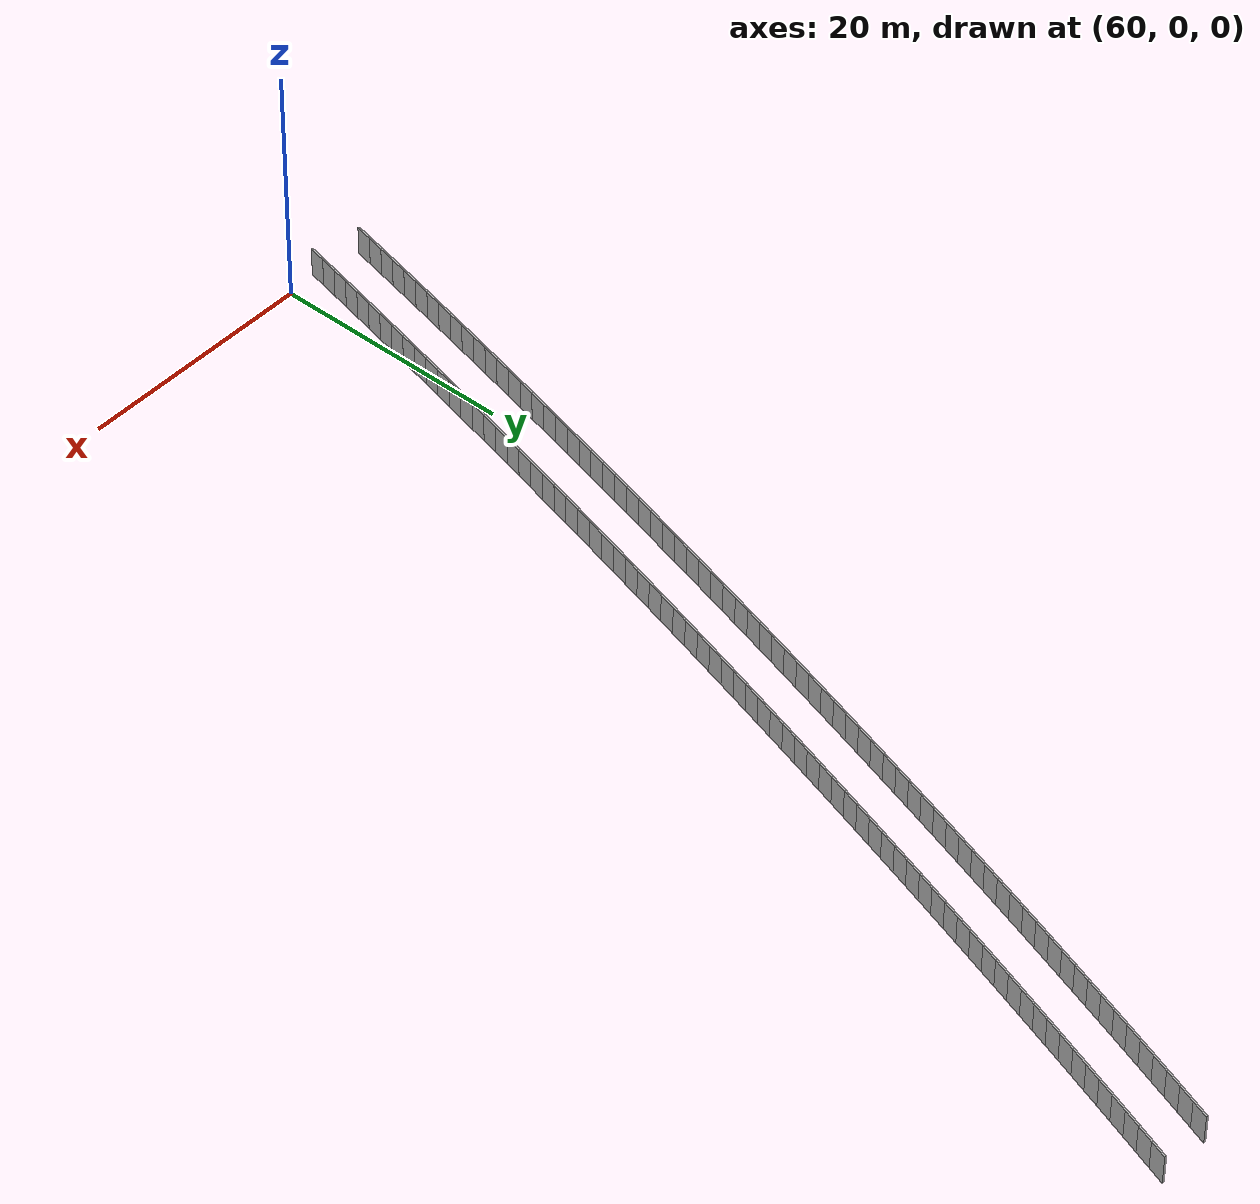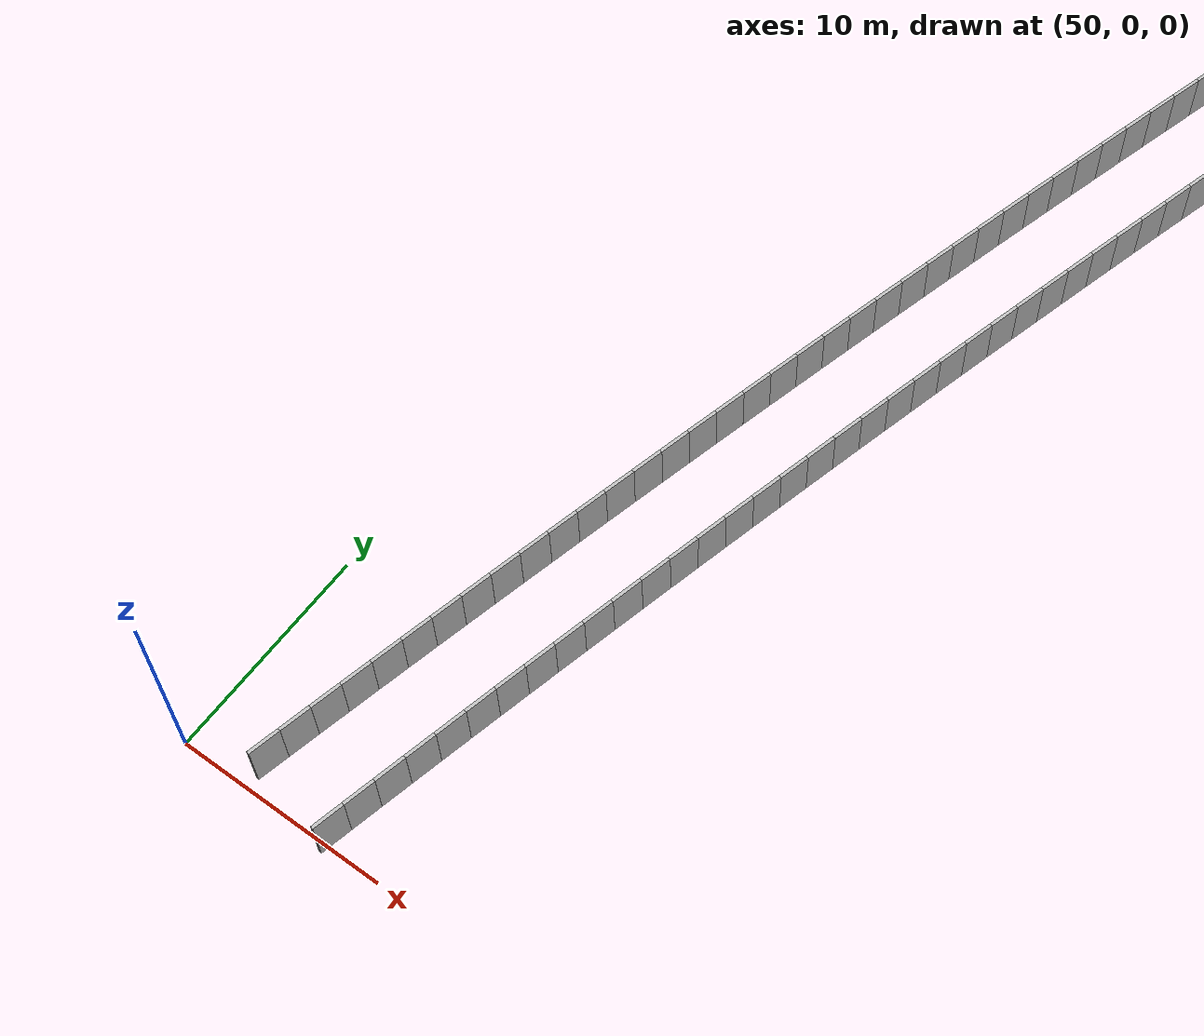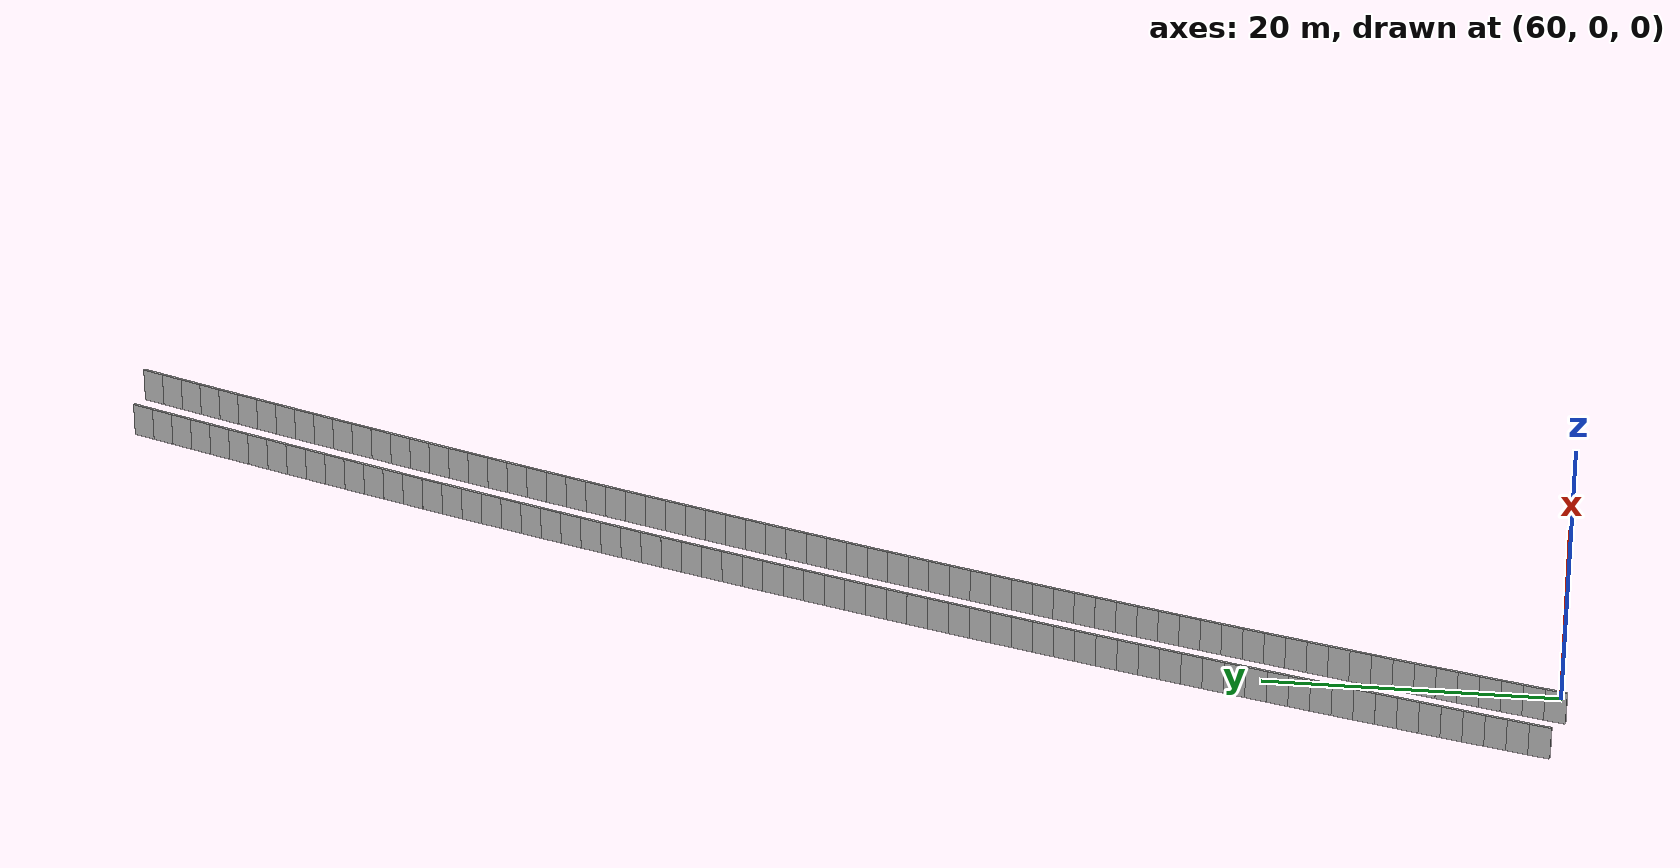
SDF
<?xml version="1.0" ?>
<sdf version="1.6">
  <model name="sps_0115">
    <pose frame="">0 0 0 0 -0 0</pose>
    <static>1</static>
    <self_collide>0</self_collide>
    <allow_auto_disable>0</allow_auto_disable>
    <link name="Wall5039">
      <kinematic>0</kinematic>
      <gravity>1</gravity>
      <self_collide>0</self_collide>
      <collision name="collision">
        <geometry>
          <box>
            <size>1.49666 0.15 2.5</size>
          </box>
        </geometry>
        <pose frame="">0 0 0 0 -0 0</pose>
      </collision>
      <visual name="visual">
        <geometry>
          <box>
            <size>1.49666 0.15 2.5</size>
          </box>
        </geometry>
        <pose frame="">0 0 0 0 -0 0</pose>
        <cast_shadows>1</cast_shadows>
        <transparency>0.0</transparency>
      </visual>
      <pose frame="">85.6731 99.6658 1.25 0 0 -1.90183</pose>
    </link>
    <link name="Wall5040">
      <kinematic>0</kinematic>
      <gravity>1</gravity>
      <self_collide>0</self_collide>
      <collision name="collision">
        <geometry>
          <box>
            <size>1.49643 0.15 2.5</size>
          </box>
        </geometry>
        <pose frame="">0 0 0 0 -0 0</pose>
      </collision>
      <visual name="visual">
        <geometry>
          <box>
            <size>1.49643 0.15 2.5</size>
          </box>
        </geometry>
        <pose frame="">0 0 0 0 -0 0</pose>
        <cast_shadows>1</cast_shadows>
        <transparency>0.0</transparency>
      </visual>
      <pose frame="">85.1879 98.2501 1.25 0 0 -1.90012</pose>
    </link>
    <link name="Wall5041">
      <kinematic>0</kinematic>
      <gravity>1</gravity>
      <self_collide>0</self_collide>
      <collision name="collision">
        <geometry>
          <box>
            <size>1.49667 0.15 2.5</size>
          </box>
        </geometry>
        <pose frame="">0 0 0 0 -0 0</pose>
      </collision>
      <visual name="visual">
        <geometry>
          <box>
            <size>1.49667 0.15 2.5</size>
          </box>
        </geometry>
        <pose frame="">0 0 0 0 -0 0</pose>
        <cast_shadows>1</cast_shadows>
        <transparency>0.0</transparency>
      </visual>
      <pose frame="">84.705 96.8336 1.25 0 0 -1.89856</pose>
    </link>
    <link name="Wall5042">
      <kinematic>0</kinematic>
      <gravity>1</gravity>
      <self_collide>0</self_collide>
      <collision name="collision">
        <geometry>
          <box>
            <size>1.49654 0.15 2.5</size>
          </box>
        </geometry>
        <pose frame="">0 0 0 0 -0 0</pose>
      </collision>
      <visual name="visual">
        <geometry>
          <box>
            <size>1.49654 0.15 2.5</size>
          </box>
        </geometry>
        <pose frame="">0 0 0 0 -0 0</pose>
        <cast_shadows>1</cast_shadows>
        <transparency>0.0</transparency>
      </visual>
      <pose frame="">84.2243 95.4163 1.25 0 0 -1.89704</pose>
    </link>
    <link name="Wall5043">
      <kinematic>0</kinematic>
      <gravity>1</gravity>
      <self_collide>0</self_collide>
      <collision name="collision">
        <geometry>
          <box>
            <size>1.49636 0.15 2.5</size>
          </box>
        </geometry>
        <pose frame="">0 0 0 0 -0 0</pose>
      </collision>
      <visual name="visual">
        <geometry>
          <box>
            <size>1.49636 0.15 2.5</size>
          </box>
        </geometry>
        <pose frame="">0 0 0 0 -0 0</pose>
        <cast_shadows>1</cast_shadows>
        <transparency>0.0</transparency>
      </visual>
      <pose frame="">83.7457 93.9984 1.25 0 0 -1.89553</pose>
    </link>
    <link name="Wall5044">
      <kinematic>0</kinematic>
      <gravity>1</gravity>
      <self_collide>0</self_collide>
      <collision name="collision">
        <geometry>
          <box>
            <size>1.49662 0.15 2.5</size>
          </box>
        </geometry>
        <pose frame="">0 0 0 0 -0 0</pose>
      </collision>
      <visual name="visual">
        <geometry>
          <box>
            <size>1.49662 0.15 2.5</size>
          </box>
        </geometry>
        <pose frame="">0 0 0 0 -0 0</pose>
        <cast_shadows>1</cast_shadows>
        <transparency>0.0</transparency>
      </visual>
      <pose frame="">83.2696 92.5797 1.25 0 0 -1.89375</pose>
    </link>
    <link name="Wall5045">
      <kinematic>0</kinematic>
      <gravity>1</gravity>
      <self_collide>0</self_collide>
      <collision name="collision">
        <geometry>
          <box>
            <size>1.49647 0.15 2.5</size>
          </box>
        </geometry>
        <pose frame="">0 0 0 0 -0 0</pose>
      </collision>
      <visual name="visual">
        <geometry>
          <box>
            <size>1.49647 0.15 2.5</size>
          </box>
        </geometry>
        <pose frame="">0 0 0 0 -0 0</pose>
        <cast_shadows>1</cast_shadows>
        <transparency>0.0</transparency>
      </visual>
      <pose frame="">82.7956 91.1602 1.25 0 0 -1.89228</pose>
    </link>
    <link name="Wall5046">
      <kinematic>0</kinematic>
      <gravity>1</gravity>
      <self_collide>0</self_collide>
      <collision name="collision">
        <geometry>
          <box>
            <size>1.49651 0.15 2.5</size>
          </box>
        </geometry>
        <pose frame="">0 0 0 0 -0 0</pose>
      </collision>
      <visual name="visual">
        <geometry>
          <box>
            <size>1.49651 0.15 2.5</size>
          </box>
        </geometry>
        <pose frame="">0 0 0 0 -0 0</pose>
        <cast_shadows>1</cast_shadows>
        <transparency>0.0</transparency>
      </visual>
      <pose frame="">82.3239 89.74 1.25 0 0 -1.89068</pose>
    </link>
    <link name="Wall5047">
      <kinematic>0</kinematic>
      <gravity>1</gravity>
      <self_collide>0</self_collide>
      <collision name="collision">
        <geometry>
          <box>
            <size>1.49651 0.15 2.5</size>
          </box>
        </geometry>
        <pose frame="">0 0 0 0 -0 0</pose>
      </collision>
      <visual name="visual">
        <geometry>
          <box>
            <size>1.49651 0.15 2.5</size>
          </box>
        </geometry>
        <pose frame="">0 0 0 0 -0 0</pose>
        <cast_shadows>1</cast_shadows>
        <transparency>0.0</transparency>
      </visual>
      <pose frame="">81.8545 88.319 1.25 0 0 -1.889</pose>
    </link>
    <link name="Wall5048">
      <kinematic>0</kinematic>
      <gravity>1</gravity>
      <self_collide>0</self_collide>
      <collision name="collision">
        <geometry>
          <box>
            <size>1.49646 0.15 2.5</size>
          </box>
        </geometry>
        <pose frame="">0 0 0 0 -0 0</pose>
      </collision>
      <visual name="visual">
        <geometry>
          <box>
            <size>1.49646 0.15 2.5</size>
          </box>
        </geometry>
        <pose frame="">0 0 0 0 -0 0</pose>
        <cast_shadows>1</cast_shadows>
        <transparency>0.0</transparency>
      </visual>
      <pose frame="">81.3874 86.8973 1.25 0 0 -1.88759</pose>
    </link>
    <link name="Wall5049">
      <kinematic>0</kinematic>
      <gravity>1</gravity>
      <self_collide>0</self_collide>
      <collision name="collision">
        <geometry>
          <box>
            <size>1.49665 0.15 2.5</size>
          </box>
        </geometry>
        <pose frame="">0 0 0 0 -0 0</pose>
      </collision>
      <visual name="visual">
        <geometry>
          <box>
            <size>1.49665 0.15 2.5</size>
          </box>
        </geometry>
        <pose frame="">0 0 0 0 -0 0</pose>
        <cast_shadows>1</cast_shadows>
        <transparency>0.0</transparency>
      </visual>
      <pose frame="">80.9224 85.4748 1.25 0 0 -1.88588</pose>
    </link>
    <link name="Wall5050">
      <kinematic>0</kinematic>
      <gravity>1</gravity>
      <self_collide>0</self_collide>
      <collision name="collision">
        <geometry>
          <box>
            <size>1.49661 0.15 2.5</size>
          </box>
        </geometry>
        <pose frame="">0 0 0 0 -0 0</pose>
      </collision>
      <visual name="visual">
        <geometry>
          <box>
            <size>1.49661 0.15 2.5</size>
          </box>
        </geometry>
        <pose frame="">0 0 0 0 -0 0</pose>
        <cast_shadows>1</cast_shadows>
        <transparency>0.0</transparency>
      </visual>
      <pose frame="">80.4596 84.0515 1.25 0 0 -1.88434</pose>
    </link>
    <link name="Wall5051">
      <kinematic>0</kinematic>
      <gravity>1</gravity>
      <self_collide>0</self_collide>
      <collision name="collision">
        <geometry>
          <box>
            <size>1.49663 0.15 2.5</size>
          </box>
        </geometry>
        <pose frame="">0 0 0 0 -0 0</pose>
      </collision>
      <visual name="visual">
        <geometry>
          <box>
            <size>1.49663 0.15 2.5</size>
          </box>
        </geometry>
        <pose frame="">0 0 0 0 -0 0</pose>
        <cast_shadows>1</cast_shadows>
        <transparency>0.0</transparency>
      </visual>
      <pose frame="">79.9991 82.6275 1.25 0 0 -1.8828</pose>
    </link>
    <link name="Wall5052">
      <kinematic>0</kinematic>
      <gravity>1</gravity>
      <self_collide>0</self_collide>
      <collision name="collision">
        <geometry>
          <box>
            <size>1.4967 0.15 2.5</size>
          </box>
        </geometry>
        <pose frame="">0 0 0 0 -0 0</pose>
      </collision>
      <visual name="visual">
        <geometry>
          <box>
            <size>1.4967 0.15 2.5</size>
          </box>
        </geometry>
        <pose frame="">0 0 0 0 -0 0</pose>
        <cast_shadows>1</cast_shadows>
        <transparency>0.0</transparency>
      </visual>
      <pose frame="">79.5409 81.2027 1.25 0 0 -1.88107</pose>
    </link>
    <link name="Wall5053">
      <kinematic>0</kinematic>
      <gravity>1</gravity>
      <self_collide>0</self_collide>
      <collision name="collision">
        <geometry>
          <box>
            <size>1.4964 0.15 2.5</size>
          </box>
        </geometry>
        <pose frame="">0 0 0 0 -0 0</pose>
      </collision>
      <visual name="visual">
        <geometry>
          <box>
            <size>1.4964 0.15 2.5</size>
          </box>
        </geometry>
        <pose frame="">0 0 0 0 -0 0</pose>
        <cast_shadows>1</cast_shadows>
        <transparency>0.0</transparency>
      </visual>
      <pose frame="">79.085 79.7773 1.25 0 0 -1.87964</pose>
    </link>
    <link name="Wall5054">
      <kinematic>0</kinematic>
      <gravity>1</gravity>
      <self_collide>0</self_collide>
      <collision name="collision">
        <geometry>
          <box>
            <size>1.49659 0.15 2.5</size>
          </box>
        </geometry>
        <pose frame="">0 0 0 0 -0 0</pose>
      </collision>
      <visual name="visual">
        <geometry>
          <box>
            <size>1.49659 0.15 2.5</size>
          </box>
        </geometry>
        <pose frame="">0 0 0 0 -0 0</pose>
        <cast_shadows>1</cast_shadows>
        <transparency>0.0</transparency>
      </visual>
      <pose frame="">78.6314 78.3512 1.25 0 0 -1.87788</pose>
    </link>
    <link name="Wall5055">
      <kinematic>0</kinematic>
      <gravity>1</gravity>
      <self_collide>0</self_collide>
      <collision name="collision">
        <geometry>
          <box>
            <size>1.49656 0.15 2.5</size>
          </box>
        </geometry>
        <pose frame="">0 0 0 0 -0 0</pose>
      </collision>
      <visual name="visual">
        <geometry>
          <box>
            <size>1.49656 0.15 2.5</size>
          </box>
        </geometry>
        <pose frame="">0 0 0 0 -0 0</pose>
        <cast_shadows>1</cast_shadows>
        <transparency>0.0</transparency>
      </visual>
      <pose frame="">78.18 76.9243 1.25 0 0 -1.87648</pose>
    </link>
    <link name="Wall5056">
      <kinematic>0</kinematic>
      <gravity>1</gravity>
      <self_collide>0</self_collide>
      <collision name="collision">
        <geometry>
          <box>
            <size>1.49643 0.15 2.5</size>
          </box>
        </geometry>
        <pose frame="">0 0 0 0 -0 0</pose>
      </collision>
      <visual name="visual">
        <geometry>
          <box>
            <size>1.49643 0.15 2.5</size>
          </box>
        </geometry>
        <pose frame="">0 0 0 0 -0 0</pose>
        <cast_shadows>1</cast_shadows>
        <transparency>0.0</transparency>
      </visual>
      <pose frame="">77.7309 75.4968 1.25 0 0 -1.87484</pose>
    </link>
    <link name="Wall5057">
      <kinematic>0</kinematic>
      <gravity>1</gravity>
      <self_collide>0</self_collide>
      <collision name="collision">
        <geometry>
          <box>
            <size>1.49653 0.15 2.5</size>
          </box>
        </geometry>
        <pose frame="">0 0 0 0 -0 0</pose>
      </collision>
      <visual name="visual">
        <geometry>
          <box>
            <size>1.49653 0.15 2.5</size>
          </box>
        </geometry>
        <pose frame="">0 0 0 0 -0 0</pose>
        <cast_shadows>1</cast_shadows>
        <transparency>0.0</transparency>
      </visual>
      <pose frame="">77.284 74.0686 1.25 0 0 -1.87328</pose>
    </link>
    <link name="Wall5058">
      <kinematic>0</kinematic>
      <gravity>1</gravity>
      <self_collide>0</self_collide>
      <collision name="collision">
        <geometry>
          <box>
            <size>1.49646 0.15 2.5</size>
          </box>
        </geometry>
        <pose frame="">0 0 0 0 -0 0</pose>
      </collision>
      <visual name="visual">
        <geometry>
          <box>
            <size>1.49646 0.15 2.5</size>
          </box>
        </geometry>
        <pose frame="">0 0 0 0 -0 0</pose>
        <cast_shadows>1</cast_shadows>
        <transparency>0.0</transparency>
      </visual>
      <pose frame="">76.8393 72.6397 1.25 0 0 -1.87163</pose>
    </link>
    <link name="Wall5059">
      <kinematic>0</kinematic>
      <gravity>1</gravity>
      <self_collide>0</self_collide>
      <collision name="collision">
        <geometry>
          <box>
            <size>1.4965 0.15 2.5</size>
          </box>
        </geometry>
        <pose frame="">0 0 0 0 -0 0</pose>
      </collision>
      <visual name="visual">
        <geometry>
          <box>
            <size>1.4965 0.15 2.5</size>
          </box>
        </geometry>
        <pose frame="">0 0 0 0 -0 0</pose>
        <cast_shadows>1</cast_shadows>
        <transparency>0.0</transparency>
      </visual>
      <pose frame="">76.3971 71.2101 1.25 0 0 -1.87004</pose>
    </link>
    <link name="Wall5060">
      <kinematic>0</kinematic>
      <gravity>1</gravity>
      <self_collide>0</self_collide>
      <collision name="collision">
        <geometry>
          <box>
            <size>1.4964 0.15 2.5</size>
          </box>
        </geometry>
        <pose frame="">0 0 0 0 -0 0</pose>
      </collision>
      <visual name="visual">
        <geometry>
          <box>
            <size>1.4964 0.15 2.5</size>
          </box>
        </geometry>
        <pose frame="">0 0 0 0 -0 0</pose>
        <cast_shadows>1</cast_shadows>
        <transparency>0.0</transparency>
      </visual>
      <pose frame="">75.9571 69.7798 1.25 0 0 -1.86844</pose>
    </link>
    <link name="Wall5061">
      <kinematic>0</kinematic>
      <gravity>1</gravity>
      <self_collide>0</self_collide>
      <collision name="collision">
        <geometry>
          <box>
            <size>1.49655 0.15 2.5</size>
          </box>
        </geometry>
        <pose frame="">0 0 0 0 -0 0</pose>
      </collision>
      <visual name="visual">
        <geometry>
          <box>
            <size>1.49655 0.15 2.5</size>
          </box>
        </geometry>
        <pose frame="">0 0 0 0 -0 0</pose>
        <cast_shadows>1</cast_shadows>
        <transparency>0.0</transparency>
      </visual>
      <pose frame="">75.5192 68.3488 1.25 0 0 -1.86696</pose>
    </link>
    <link name="Wall5062">
      <kinematic>0</kinematic>
      <gravity>1</gravity>
      <self_collide>0</self_collide>
      <collision name="collision">
        <geometry>
          <box>
            <size>1.49662 0.15 2.5</size>
          </box>
        </geometry>
        <pose frame="">0 0 0 0 -0 0</pose>
      </collision>
      <visual name="visual">
        <geometry>
          <box>
            <size>1.49662 0.15 2.5</size>
          </box>
        </geometry>
        <pose frame="">0 0 0 0 -0 0</pose>
        <cast_shadows>1</cast_shadows>
        <transparency>0.0</transparency>
      </visual>
      <pose frame="">75.0837 66.917 1.25 0 0 -1.86528</pose>
    </link>
    <link name="Wall5063">
      <kinematic>0</kinematic>
      <gravity>1</gravity>
      <self_collide>0</self_collide>
      <collision name="collision">
        <geometry>
          <box>
            <size>1.49658 0.15 2.5</size>
          </box>
        </geometry>
        <pose frame="">0 0 0 0 -0 0</pose>
      </collision>
      <visual name="visual">
        <geometry>
          <box>
            <size>1.49658 0.15 2.5</size>
          </box>
        </geometry>
        <pose frame="">0 0 0 0 -0 0</pose>
        <cast_shadows>1</cast_shadows>
        <transparency>0.0</transparency>
      </visual>
      <pose frame="">74.6504 65.4845 1.25 0 0 -1.8638</pose>
    </link>
    <link name="Wall5064">
      <kinematic>0</kinematic>
      <gravity>1</gravity>
      <self_collide>0</self_collide>
      <collision name="collision">
        <geometry>
          <box>
            <size>1.49645 0.15 2.5</size>
          </box>
        </geometry>
        <pose frame="">0 0 0 0 -0 0</pose>
      </collision>
      <visual name="visual">
        <geometry>
          <box>
            <size>1.49645 0.15 2.5</size>
          </box>
        </geometry>
        <pose frame="">0 0 0 0 -0 0</pose>
        <cast_shadows>1</cast_shadows>
        <transparency>0.0</transparency>
      </visual>
      <pose frame="">74.2194 64.0514 1.25 0 0 -1.86208</pose>
    </link>
    <link name="Wall5065">
      <kinematic>0</kinematic>
      <gravity>1</gravity>
      <self_collide>0</self_collide>
      <collision name="collision">
        <geometry>
          <box>
            <size>1.49659 0.15 2.5</size>
          </box>
        </geometry>
        <pose frame="">0 0 0 0 -0 0</pose>
      </collision>
      <visual name="visual">
        <geometry>
          <box>
            <size>1.49659 0.15 2.5</size>
          </box>
        </geometry>
        <pose frame="">0 0 0 0 -0 0</pose>
        <cast_shadows>1</cast_shadows>
        <transparency>0.0</transparency>
      </visual>
      <pose frame="">73.7907 62.6176 1.25 0 0 -1.86056</pose>
    </link>
    <link name="Wall5066">
      <kinematic>0</kinematic>
      <gravity>1</gravity>
      <self_collide>0</self_collide>
      <collision name="collision">
        <geometry>
          <box>
            <size>1.49649 0.15 2.5</size>
          </box>
        </geometry>
        <pose frame="">0 0 0 0 -0 0</pose>
      </collision>
      <visual name="visual">
        <geometry>
          <box>
            <size>1.49649 0.15 2.5</size>
          </box>
        </geometry>
        <pose frame="">0 0 0 0 -0 0</pose>
        <cast_shadows>1</cast_shadows>
        <transparency>0.0</transparency>
      </visual>
      <pose frame="">73.3642 61.1831 1.25 0 0 -1.85905</pose>
    </link>
    <link name="Wall5067">
      <kinematic>0</kinematic>
      <gravity>1</gravity>
      <self_collide>0</self_collide>
      <collision name="collision">
        <geometry>
          <box>
            <size>1.49652 0.15 2.5</size>
          </box>
        </geometry>
        <pose frame="">0 0 0 0 -0 0</pose>
      </collision>
      <visual name="visual">
        <geometry>
          <box>
            <size>1.49652 0.15 2.5</size>
          </box>
        </geometry>
        <pose frame="">0 0 0 0 -0 0</pose>
        <cast_shadows>1</cast_shadows>
        <transparency>0.0</transparency>
      </visual>
      <pose frame="">72.9398 59.748 1.25 0 0 -1.85751</pose>
    </link>
    <link name="Wall5068">
      <kinematic>0</kinematic>
      <gravity>1</gravity>
      <self_collide>0</self_collide>
      <collision name="collision">
        <geometry>
          <box>
            <size>1.49654 0.15 2.5</size>
          </box>
        </geometry>
        <pose frame="">0 0 0 0 -0 0</pose>
      </collision>
      <visual name="visual">
        <geometry>
          <box>
            <size>1.49654 0.15 2.5</size>
          </box>
        </geometry>
        <pose frame="">0 0 0 0 -0 0</pose>
        <cast_shadows>1</cast_shadows>
        <transparency>0.0</transparency>
      </visual>
      <pose frame="">72.5179 58.3122 1.25 0 0 -1.85568</pose>
    </link>
    <link name="Wall5069">
      <kinematic>0</kinematic>
      <gravity>1</gravity>
      <self_collide>0</self_collide>
      <collision name="collision">
        <geometry>
          <box>
            <size>1.4965 0.15 2.5</size>
          </box>
        </geometry>
        <pose frame="">0 0 0 0 -0 0</pose>
      </collision>
      <visual name="visual">
        <geometry>
          <box>
            <size>1.4965 0.15 2.5</size>
          </box>
        </geometry>
        <pose frame="">0 0 0 0 -0 0</pose>
        <cast_shadows>1</cast_shadows>
        <transparency>0.0</transparency>
      </visual>
      <pose frame="">72.0983 56.8757 1.25 0 0 -1.85428</pose>
    </link>
    <link name="Wall5070">
      <kinematic>0</kinematic>
      <gravity>1</gravity>
      <self_collide>0</self_collide>
      <collision name="collision">
        <geometry>
          <box>
            <size>1.49648 0.15 2.5</size>
          </box>
        </geometry>
        <pose frame="">0 0 0 0 -0 0</pose>
      </collision>
      <visual name="visual">
        <geometry>
          <box>
            <size>1.49648 0.15 2.5</size>
          </box>
        </geometry>
        <pose frame="">0 0 0 0 -0 0</pose>
        <cast_shadows>1</cast_shadows>
        <transparency>0.0</transparency>
      </visual>
      <pose frame="">71.681 55.4386 1.25 0 0 -1.85263</pose>
    </link>
    <link name="Wall5071">
      <kinematic>0</kinematic>
      <gravity>1</gravity>
      <self_collide>0</self_collide>
      <collision name="collision">
        <geometry>
          <box>
            <size>1.4964 0.15 2.5</size>
          </box>
        </geometry>
        <pose frame="">0 0 0 0 -0 0</pose>
      </collision>
      <visual name="visual">
        <geometry>
          <box>
            <size>1.4964 0.15 2.5</size>
          </box>
        </geometry>
        <pose frame="">0 0 0 0 -0 0</pose>
        <cast_shadows>1</cast_shadows>
        <transparency>0.0</transparency>
      </visual>
      <pose frame="">71.2659 54.0009 1.25 0 0 -1.85112</pose>
    </link>
    <link name="Wall5072">
      <kinematic>0</kinematic>
      <gravity>1</gravity>
      <self_collide>0</self_collide>
      <collision name="collision">
        <geometry>
          <box>
            <size>1.4965 0.15 2.5</size>
          </box>
        </geometry>
        <pose frame="">0 0 0 0 -0 0</pose>
      </collision>
      <visual name="visual">
        <geometry>
          <box>
            <size>1.4965 0.15 2.5</size>
          </box>
        </geometry>
        <pose frame="">0 0 0 0 -0 0</pose>
        <cast_shadows>1</cast_shadows>
        <transparency>0.0</transparency>
      </visual>
      <pose frame="">70.853 52.5625 1.25 0 0 -1.84944</pose>
    </link>
    <link name="Wall5073">
      <kinematic>0</kinematic>
      <gravity>1</gravity>
      <self_collide>0</self_collide>
      <collision name="collision">
        <geometry>
          <box>
            <size>1.49665 0.15 2.5</size>
          </box>
        </geometry>
        <pose frame="">0 0 0 0 -0 0</pose>
      </collision>
      <visual name="visual">
        <geometry>
          <box>
            <size>1.49665 0.15 2.5</size>
          </box>
        </geometry>
        <pose frame="">0 0 0 0 -0 0</pose>
        <cast_shadows>1</cast_shadows>
        <transparency>0.0</transparency>
      </visual>
      <pose frame="">70.4426 51.1233 1.25 0 0 -1.84785</pose>
    </link>
    <link name="Wall5074">
      <kinematic>0</kinematic>
      <gravity>1</gravity>
      <self_collide>0</self_collide>
      <collision name="collision">
        <geometry>
          <box>
            <size>1.49648 0.15 2.5</size>
          </box>
        </geometry>
        <pose frame="">0 0 0 0 -0 0</pose>
      </collision>
      <visual name="visual">
        <geometry>
          <box>
            <size>1.49648 0.15 2.5</size>
          </box>
        </geometry>
        <pose frame="">0 0 0 0 -0 0</pose>
        <cast_shadows>1</cast_shadows>
        <transparency>0.0</transparency>
      </visual>
      <pose frame="">70.0343 49.6835 1.25 0 0 -1.8464</pose>
    </link>
    <link name="Wall5075">
      <kinematic>0</kinematic>
      <gravity>1</gravity>
      <self_collide>0</self_collide>
      <collision name="collision">
        <geometry>
          <box>
            <size>1.49658 0.15 2.5</size>
          </box>
        </geometry>
        <pose frame="">0 0 0 0 -0 0</pose>
      </collision>
      <visual name="visual">
        <geometry>
          <box>
            <size>1.49658 0.15 2.5</size>
          </box>
        </geometry>
        <pose frame="">0 0 0 0 -0 0</pose>
        <cast_shadows>1</cast_shadows>
        <transparency>0.0</transparency>
      </visual>
      <pose frame="">69.6283 48.2431 1.25 0 0 -1.84468</pose>
    </link>
    <link name="Wall5076">
      <kinematic>0</kinematic>
      <gravity>1</gravity>
      <self_collide>0</self_collide>
      <collision name="collision">
        <geometry>
          <box>
            <size>1.49657 0.15 2.5</size>
          </box>
        </geometry>
        <pose frame="">0 0 0 0 -0 0</pose>
      </collision>
      <visual name="visual">
        <geometry>
          <box>
            <size>1.49657 0.15 2.5</size>
          </box>
        </geometry>
        <pose frame="">0 0 0 0 -0 0</pose>
        <cast_shadows>1</cast_shadows>
        <transparency>0.0</transparency>
      </visual>
      <pose frame="">69.2246 46.802 1.25 0 0 -1.84316</pose>
    </link>
    <link name="Wall5077">
      <kinematic>0</kinematic>
      <gravity>1</gravity>
      <self_collide>0</self_collide>
      <collision name="collision">
        <geometry>
          <box>
            <size>1.49652 0.15 2.5</size>
          </box>
        </geometry>
        <pose frame="">0 0 0 0 -0 0</pose>
      </collision>
      <visual name="visual">
        <geometry>
          <box>
            <size>1.49652 0.15 2.5</size>
          </box>
        </geometry>
        <pose frame="">0 0 0 0 -0 0</pose>
        <cast_shadows>1</cast_shadows>
        <transparency>0.0</transparency>
      </visual>
      <pose frame="">68.8232 45.3603 1.25 0 0 -1.84152</pose>
    </link>
    <link name="Wall5078">
      <kinematic>0</kinematic>
      <gravity>1</gravity>
      <self_collide>0</self_collide>
      <collision name="collision">
        <geometry>
          <box>
            <size>1.49652 0.15 2.5</size>
          </box>
        </geometry>
        <pose frame="">0 0 0 0 -0 0</pose>
      </collision>
      <visual name="visual">
        <geometry>
          <box>
            <size>1.49652 0.15 2.5</size>
          </box>
        </geometry>
        <pose frame="">0 0 0 0 -0 0</pose>
        <cast_shadows>1</cast_shadows>
        <transparency>0.0</transparency>
      </visual>
      <pose frame="">68.4241 43.918 1.25 0 0 -1.83999</pose>
    </link>
    <link name="Wall5079">
      <kinematic>0</kinematic>
      <gravity>1</gravity>
      <self_collide>0</self_collide>
      <collision name="collision">
        <geometry>
          <box>
            <size>1.49642 0.15 2.5</size>
          </box>
        </geometry>
        <pose frame="">0 0 0 0 -0 0</pose>
      </collision>
      <visual name="visual">
        <geometry>
          <box>
            <size>1.49642 0.15 2.5</size>
          </box>
        </geometry>
        <pose frame="">0 0 0 0 -0 0</pose>
        <cast_shadows>1</cast_shadows>
        <transparency>0.0</transparency>
      </visual>
      <pose frame="">68.0272 42.4751 1.25 0 0 -1.83836</pose>
    </link>
    <link name="Wall5080">
      <kinematic>0</kinematic>
      <gravity>1</gravity>
      <self_collide>0</self_collide>
      <collision name="collision">
        <geometry>
          <box>
            <size>1.49665 0.15 2.5</size>
          </box>
        </geometry>
        <pose frame="">0 0 0 0 -0 0</pose>
      </collision>
      <visual name="visual">
        <geometry>
          <box>
            <size>1.49665 0.15 2.5</size>
          </box>
        </geometry>
        <pose frame="">0 0 0 0 -0 0</pose>
        <cast_shadows>1</cast_shadows>
        <transparency>0.0</transparency>
      </visual>
      <pose frame="">67.6327 41.0315 1.25 0 0 -1.83676</pose>
    </link>
    <link name="Wall5081">
      <kinematic>0</kinematic>
      <gravity>1</gravity>
      <self_collide>0</self_collide>
      <collision name="collision">
        <geometry>
          <box>
            <size>1.49643 0.15 2.5</size>
          </box>
        </geometry>
        <pose frame="">0 0 0 0 -0 0</pose>
      </collision>
      <visual name="visual">
        <geometry>
          <box>
            <size>1.49643 0.15 2.5</size>
          </box>
        </geometry>
        <pose frame="">0 0 0 0 -0 0</pose>
        <cast_shadows>1</cast_shadows>
        <transparency>0.0</transparency>
      </visual>
      <pose frame="">67.2405 39.5873 1.25 0 0 -1.83527</pose>
    </link>
    <link name="Wall5082">
      <kinematic>0</kinematic>
      <gravity>1</gravity>
      <self_collide>0</self_collide>
      <collision name="collision">
        <geometry>
          <box>
            <size>1.49635 0.15 2.5</size>
          </box>
        </geometry>
        <pose frame="">0 0 0 0 -0 0</pose>
      </collision>
      <visual name="visual">
        <geometry>
          <box>
            <size>1.49635 0.15 2.5</size>
          </box>
        </geometry>
        <pose frame="">0 0 0 0 -0 0</pose>
        <cast_shadows>1</cast_shadows>
        <transparency>0.0</transparency>
      </visual>
      <pose frame="">66.8505 38.1426 1.25 0 0 -1.83368</pose>
    </link>
    <link name="Wall5083">
      <kinematic>0</kinematic>
      <gravity>1</gravity>
      <self_collide>0</self_collide>
      <collision name="collision">
        <geometry>
          <box>
            <size>1.4966 0.15 2.5</size>
          </box>
        </geometry>
        <pose frame="">0 0 0 0 -0 0</pose>
      </collision>
      <visual name="visual">
        <geometry>
          <box>
            <size>1.4966 0.15 2.5</size>
          </box>
        </geometry>
        <pose frame="">0 0 0 0 -0 0</pose>
        <cast_shadows>1</cast_shadows>
        <transparency>0.0</transparency>
      </visual>
      <pose frame="">66.4627 36.6972 1.25 0 0 -1.83208</pose>
    </link>
    <link name="Wall5084">
      <kinematic>0</kinematic>
      <gravity>1</gravity>
      <self_collide>0</self_collide>
      <collision name="collision">
        <geometry>
          <box>
            <size>1.49656 0.15 2.5</size>
          </box>
        </geometry>
        <pose frame="">0 0 0 0 -0 0</pose>
      </collision>
      <visual name="visual">
        <geometry>
          <box>
            <size>1.49656 0.15 2.5</size>
          </box>
        </geometry>
        <pose frame="">0 0 0 0 -0 0</pose>
        <cast_shadows>1</cast_shadows>
        <transparency>0.0</transparency>
      </visual>
      <pose frame="">66.0774 35.2511 1.25 0 0 -1.8304</pose>
    </link>
    <link name="Wall5085">
      <kinematic>0</kinematic>
      <gravity>1</gravity>
      <self_collide>0</self_collide>
      <collision name="collision">
        <geometry>
          <box>
            <size>1.49642 0.15 2.5</size>
          </box>
        </geometry>
        <pose frame="">0 0 0 0 -0 0</pose>
      </collision>
      <visual name="visual">
        <geometry>
          <box>
            <size>1.49642 0.15 2.5</size>
          </box>
        </geometry>
        <pose frame="">0 0 0 0 -0 0</pose>
        <cast_shadows>1</cast_shadows>
        <transparency>0.0</transparency>
      </visual>
      <pose frame="">65.6943 33.8045 1.25 0 0 -1.82894</pose>
    </link>
    <link name="Wall5086">
      <kinematic>0</kinematic>
      <gravity>1</gravity>
      <self_collide>0</self_collide>
      <collision name="collision">
        <geometry>
          <box>
            <size>1.49669 0.15 2.5</size>
          </box>
        </geometry>
        <pose frame="">0 0 0 0 -0 0</pose>
      </collision>
      <visual name="visual">
        <geometry>
          <box>
            <size>1.49669 0.15 2.5</size>
          </box>
        </geometry>
        <pose frame="">0 0 0 0 -0 0</pose>
        <cast_shadows>1</cast_shadows>
        <transparency>0.0</transparency>
      </visual>
      <pose frame="">65.3135 32.3572 1.25 0 0 -1.82721</pose>
    </link>
    <link name="Wall5087">
      <kinematic>0</kinematic>
      <gravity>1</gravity>
      <self_collide>0</self_collide>
      <collision name="collision">
        <geometry>
          <box>
            <size>1.49638 0.15 2.5</size>
          </box>
        </geometry>
        <pose frame="">0 0 0 0 -0 0</pose>
      </collision>
      <visual name="visual">
        <geometry>
          <box>
            <size>1.49638 0.15 2.5</size>
          </box>
        </geometry>
        <pose frame="">0 0 0 0 -0 0</pose>
        <cast_shadows>1</cast_shadows>
        <transparency>0.0</transparency>
      </visual>
      <pose frame="">64.935 30.9093 1.25 0 0 -1.82579</pose>
    </link>
    <link name="Wall5088">
      <kinematic>0</kinematic>
      <gravity>1</gravity>
      <self_collide>0</self_collide>
      <collision name="collision">
        <geometry>
          <box>
            <size>1.4966 0.15 2.5</size>
          </box>
        </geometry>
        <pose frame="">0 0 0 0 -0 0</pose>
      </collision>
      <visual name="visual">
        <geometry>
          <box>
            <size>1.4966 0.15 2.5</size>
          </box>
        </geometry>
        <pose frame="">0 0 0 0 -0 0</pose>
        <cast_shadows>1</cast_shadows>
        <transparency>0.0</transparency>
      </visual>
      <pose frame="">64.5587 29.4609 1.25 0 0 -1.82406</pose>
    </link>
    <link name="Wall5089">
      <kinematic>0</kinematic>
      <gravity>1</gravity>
      <self_collide>0</self_collide>
      <collision name="collision">
        <geometry>
          <box>
            <size>1.49658 0.15 2.5</size>
          </box>
        </geometry>
        <pose frame="">0 0 0 0 -0 0</pose>
      </collision>
      <visual name="visual">
        <geometry>
          <box>
            <size>1.49658 0.15 2.5</size>
          </box>
        </geometry>
        <pose frame="">0 0 0 0 -0 0</pose>
        <cast_shadows>1</cast_shadows>
        <transparency>0.0</transparency>
      </visual>
      <pose frame="">64.1848 28.0118 1.25 0 0 -1.82255</pose>
    </link>
    <link name="Wall5090">
      <kinematic>0</kinematic>
      <gravity>1</gravity>
      <self_collide>0</self_collide>
      <collision name="collision">
        <geometry>
          <box>
            <size>1.49639 0.15 2.5</size>
          </box>
        </geometry>
        <pose frame="">0 0 0 0 -0 0</pose>
      </collision>
      <visual name="visual">
        <geometry>
          <box>
            <size>1.49639 0.15 2.5</size>
          </box>
        </geometry>
        <pose frame="">0 0 0 0 -0 0</pose>
        <cast_shadows>1</cast_shadows>
        <transparency>0.0</transparency>
      </visual>
      <pose frame="">63.8131 26.5622 1.25 0 0 -1.82107</pose>
    </link>
    <link name="Wall5091">
      <kinematic>0</kinematic>
      <gravity>1</gravity>
      <self_collide>0</self_collide>
      <collision name="collision">
        <geometry>
          <box>
            <size>1.49657 0.15 2.5</size>
          </box>
        </geometry>
        <pose frame="">0 0 0 0 -0 0</pose>
      </collision>
      <visual name="visual">
        <geometry>
          <box>
            <size>1.49657 0.15 2.5</size>
          </box>
        </geometry>
        <pose frame="">0 0 0 0 -0 0</pose>
        <cast_shadows>1</cast_shadows>
        <transparency>0.0</transparency>
      </visual>
      <pose frame="">63.4438 25.112 1.25 0 0 -1.81923</pose>
    </link>
    <link name="Wall5092">
      <kinematic>0</kinematic>
      <gravity>1</gravity>
      <self_collide>0</self_collide>
      <collision name="collision">
        <geometry>
          <box>
            <size>1.49643 0.15 2.5</size>
          </box>
        </geometry>
        <pose frame="">0 0 0 0 -0 0</pose>
      </collision>
      <visual name="visual">
        <geometry>
          <box>
            <size>1.49643 0.15 2.5</size>
          </box>
        </geometry>
        <pose frame="">0 0 0 0 -0 0</pose>
        <cast_shadows>1</cast_shadows>
        <transparency>0.0</transparency>
      </visual>
      <pose frame="">63.0769 23.6612 1.25 0 0 -1.81786</pose>
    </link>
    <link name="Wall5093">
      <kinematic>0</kinematic>
      <gravity>1</gravity>
      <self_collide>0</self_collide>
      <collision name="collision">
        <geometry>
          <box>
            <size>1.49663 0.15 2.5</size>
          </box>
        </geometry>
        <pose frame="">0 0 0 0 -0 0</pose>
      </collision>
      <visual name="visual">
        <geometry>
          <box>
            <size>1.49663 0.15 2.5</size>
          </box>
        </geometry>
        <pose frame="">0 0 0 0 -0 0</pose>
        <cast_shadows>1</cast_shadows>
        <transparency>0.0</transparency>
      </visual>
      <pose frame="">62.7121 22.2098 1.25 0 0 -1.81623</pose>
    </link>
    <link name="Wall5094">
      <kinematic>0</kinematic>
      <gravity>1</gravity>
      <self_collide>0</self_collide>
      <collision name="collision">
        <geometry>
          <box>
            <size>1.49663 0.15 2.5</size>
          </box>
        </geometry>
        <pose frame="">0 0 0 0 -0 0</pose>
      </collision>
      <visual name="visual">
        <geometry>
          <box>
            <size>1.49663 0.15 2.5</size>
          </box>
        </geometry>
        <pose frame="">0 0 0 0 -0 0</pose>
        <cast_shadows>1</cast_shadows>
        <transparency>0.0</transparency>
      </visual>
      <pose frame="">62.3496 20.7577 1.25 0 0 -1.81455</pose>
    </link>
    <link name="Wall5095">
      <kinematic>0</kinematic>
      <gravity>1</gravity>
      <self_collide>0</self_collide>
      <collision name="collision">
        <geometry>
          <box>
            <size>1.49651 0.15 2.5</size>
          </box>
        </geometry>
        <pose frame="">0 0 0 0 -0 0</pose>
      </collision>
      <visual name="visual">
        <geometry>
          <box>
            <size>1.49651 0.15 2.5</size>
          </box>
        </geometry>
        <pose frame="">0 0 0 0 -0 0</pose>
        <cast_shadows>1</cast_shadows>
        <transparency>0.0</transparency>
      </visual>
      <pose frame="">61.9896 19.3051 1.25 0 0 -1.81302</pose>
    </link>
    <link name="Wall5096">
      <kinematic>0</kinematic>
      <gravity>1</gravity>
      <self_collide>0</self_collide>
      <collision name="collision">
        <geometry>
          <box>
            <size>1.49648 0.15 2.5</size>
          </box>
        </geometry>
        <pose frame="">0 0 0 0 -0 0</pose>
      </collision>
      <visual name="visual">
        <geometry>
          <box>
            <size>1.49648 0.15 2.5</size>
          </box>
        </geometry>
        <pose frame="">0 0 0 0 -0 0</pose>
        <cast_shadows>1</cast_shadows>
        <transparency>0.0</transparency>
      </visual>
      <pose frame="">61.6318 17.852 1.25 0 0 -1.81142</pose>
    </link>
    <link name="Wall5097">
      <kinematic>0</kinematic>
      <gravity>1</gravity>
      <self_collide>0</self_collide>
      <collision name="collision">
        <geometry>
          <box>
            <size>1.4966 0.15 2.5</size>
          </box>
        </geometry>
        <pose frame="">0 0 0 0 -0 0</pose>
      </collision>
      <visual name="visual">
        <geometry>
          <box>
            <size>1.4966 0.15 2.5</size>
          </box>
        </geometry>
        <pose frame="">0 0 0 0 -0 0</pose>
        <cast_shadows>1</cast_shadows>
        <transparency>0.0</transparency>
      </visual>
      <pose frame="">61.2763 16.3983 1.25 0 0 -1.80985</pose>
    </link>
    <link name="Wall5098">
      <kinematic>0</kinematic>
      <gravity>1</gravity>
      <self_collide>0</self_collide>
      <collision name="collision">
        <geometry>
          <box>
            <size>1.49641 0.15 2.5</size>
          </box>
        </geometry>
        <pose frame="">0 0 0 0 -0 0</pose>
      </collision>
      <visual name="visual">
        <geometry>
          <box>
            <size>1.49641 0.15 2.5</size>
          </box>
        </geometry>
        <pose frame="">0 0 0 0 -0 0</pose>
        <cast_shadows>1</cast_shadows>
        <transparency>0.0</transparency>
      </visual>
      <pose frame="">60.9231 14.9441 1.25 0 0 -1.80829</pose>
    </link>
    <link name="Wall5099">
      <kinematic>0</kinematic>
      <gravity>1</gravity>
      <self_collide>0</self_collide>
      <collision name="collision">
        <geometry>
          <box>
            <size>1.49665 0.15 2.5</size>
          </box>
        </geometry>
        <pose frame="">0 0 0 0 -0 0</pose>
      </collision>
      <visual name="visual">
        <geometry>
          <box>
            <size>1.49665 0.15 2.5</size>
          </box>
        </geometry>
        <pose frame="">0 0 0 0 -0 0</pose>
        <cast_shadows>1</cast_shadows>
        <transparency>0.0</transparency>
      </visual>
      <pose frame="">60.5721 13.4893 1.25 0 0 -1.8067</pose>
    </link>
    <link name="Wall5100">
      <kinematic>0</kinematic>
      <gravity>1</gravity>
      <self_collide>0</self_collide>
      <collision name="collision">
        <geometry>
          <box>
            <size>1.49649 0.15 2.5</size>
          </box>
        </geometry>
        <pose frame="">0 0 0 0 -0 0</pose>
      </collision>
      <visual name="visual">
        <geometry>
          <box>
            <size>1.49649 0.15 2.5</size>
          </box>
        </geometry>
        <pose frame="">0 0 0 0 -0 0</pose>
        <cast_shadows>1</cast_shadows>
        <transparency>0.0</transparency>
      </visual>
      <pose frame="">60.2234 12.0339 1.25 0 0 -1.80521</pose>
    </link>
    <link name="Wall5101">
      <kinematic>0</kinematic>
      <gravity>1</gravity>
      <self_collide>0</self_collide>
      <collision name="collision">
        <geometry>
          <box>
            <size>1.4966 0.15 2.5</size>
          </box>
        </geometry>
        <pose frame="">0 0 0 0 -0 0</pose>
      </collision>
      <visual name="visual">
        <geometry>
          <box>
            <size>1.4966 0.15 2.5</size>
          </box>
        </geometry>
        <pose frame="">0 0 0 0 -0 0</pose>
        <cast_shadows>1</cast_shadows>
        <transparency>0.0</transparency>
      </visual>
      <pose frame="">59.877 10.578 1.25 0 0 -1.80356</pose>
    </link>
    <link name="Wall5102">
      <kinematic>0</kinematic>
      <gravity>1</gravity>
      <self_collide>0</self_collide>
      <collision name="collision">
        <geometry>
          <box>
            <size>1.49639 0.15 2.5</size>
          </box>
        </geometry>
        <pose frame="">0 0 0 0 -0 0</pose>
      </collision>
      <visual name="visual">
        <geometry>
          <box>
            <size>1.49639 0.15 2.5</size>
          </box>
        </geometry>
        <pose frame="">0 0 0 0 -0 0</pose>
        <cast_shadows>1</cast_shadows>
        <transparency>0.0</transparency>
      </visual>
      <pose frame="">59.533 9.12157 1.25 0 0 -1.80192</pose>
    </link>
    <link name="Wall5103">
      <kinematic>0</kinematic>
      <gravity>1</gravity>
      <self_collide>0</self_collide>
      <collision name="collision">
        <geometry>
          <box>
            <size>1.49643 0.15 2.5</size>
          </box>
        </geometry>
        <pose frame="">0 0 0 0 -0 0</pose>
      </collision>
      <visual name="visual">
        <geometry>
          <box>
            <size>1.49643 0.15 2.5</size>
          </box>
        </geometry>
        <pose frame="">0 0 0 0 -0 0</pose>
        <cast_shadows>1</cast_shadows>
        <transparency>0.0</transparency>
      </visual>
      <pose frame="">59.1914 7.66469 1.25 0 0 -1.8004</pose>
    </link>
    <link name="Wall5104">
      <kinematic>0</kinematic>
      <gravity>1</gravity>
      <self_collide>0</self_collide>
      <collision name="collision">
        <geometry>
          <box>
            <size>1.49654 0.15 2.5</size>
          </box>
        </geometry>
        <pose frame="">0 0 0 0 -0 0</pose>
      </collision>
      <visual name="visual">
        <geometry>
          <box>
            <size>1.49654 0.15 2.5</size>
          </box>
        </geometry>
        <pose frame="">0 0 0 0 -0 0</pose>
        <cast_shadows>1</cast_shadows>
        <transparency>0.0</transparency>
      </visual>
      <pose frame="">58.852 6.2072 1.25 0 0 -1.79875</pose>
    </link>
    <link name="Wall5105">
      <kinematic>0</kinematic>
      <gravity>1</gravity>
      <self_collide>0</self_collide>
      <collision name="collision">
        <geometry>
          <box>
            <size>1.49654 0.15 2.5</size>
          </box>
        </geometry>
        <pose frame="">0 0 0 0 -0 0</pose>
      </collision>
      <visual name="visual">
        <geometry>
          <box>
            <size>1.49654 0.15 2.5</size>
          </box>
        </geometry>
        <pose frame="">0 0 0 0 -0 0</pose>
        <cast_shadows>1</cast_shadows>
        <transparency>0.0</transparency>
      </visual>
      <pose frame="">58.515 4.7491 1.25 0 0 -1.79712</pose>
    </link>
    <link name="Wall5106">
      <kinematic>0</kinematic>
      <gravity>1</gravity>
      <self_collide>0</self_collide>
      <collision name="collision">
        <geometry>
          <box>
            <size>1.49646 0.15 2.5</size>
          </box>
        </geometry>
        <pose frame="">0 0 0 0 -0 0</pose>
      </collision>
      <visual name="visual">
        <geometry>
          <box>
            <size>1.49646 0.15 2.5</size>
          </box>
        </geometry>
        <pose frame="">0 0 0 0 -0 0</pose>
        <cast_shadows>1</cast_shadows>
        <transparency>0.0</transparency>
      </visual>
      <pose frame="">58.1803 3.29051 1.25 0 0 -1.79562</pose>
    </link>
    <link name="Wall5107">
      <kinematic>0</kinematic>
      <gravity>1</gravity>
      <self_collide>0</self_collide>
      <collision name="collision">
        <geometry>
          <box>
            <size>1.49657 0.15 2.5</size>
          </box>
        </geometry>
        <pose frame="">0 0 0 0 -0 0</pose>
      </collision>
      <visual name="visual">
        <geometry>
          <box>
            <size>1.49657 0.15 2.5</size>
          </box>
        </geometry>
        <pose frame="">0 0 0 0 -0 0</pose>
        <cast_shadows>1</cast_shadows>
        <transparency>0.0</transparency>
      </visual>
      <pose frame="">57.8477 1.8314 1.25 0 0 -1.7941</pose>
    </link>
    <link name="Wall5108">
      <kinematic>0</kinematic>
      <gravity>1</gravity>
      <self_collide>0</self_collide>
      <collision name="collision">
        <geometry>
          <box>
            <size>1.49659 0.15 2.5</size>
          </box>
        </geometry>
        <pose frame="">0 0 0 0 -0 0</pose>
      </collision>
      <visual name="visual">
        <geometry>
          <box>
            <size>1.49659 0.15 2.5</size>
          </box>
        </geometry>
        <pose frame="">0 0 0 0 -0 0</pose>
        <cast_shadows>1</cast_shadows>
        <transparency>0.0</transparency>
      </visual>
      <pose frame="">57.5176 0.371688 1.25 0 0 -1.7923</pose>
    </link>
    <link name="Wall6836">
      <kinematic>0</kinematic>
      <gravity>1</gravity>
      <self_collide>0</self_collide>
      <collision name="collision">
        <geometry>
          <box>
            <size>1.50305 0.15 2.5</size>
          </box>
        </geometry>
        <pose frame="">0 0 0 0 -0 0</pose>
      </collision>
      <visual name="visual">
        <geometry>
          <box>
            <size>1.50305 0.15 2.5</size>
          </box>
        </geometry>
        <pose frame="">0 0 0 0 -0 0</pose>
        <cast_shadows>1</cast_shadows>
        <transparency>0.0</transparency>
      </visual>
      <pose frame="">81.2711 99.5892 1.25 0 0 -1.9002</pose>
    </link>
    <link name="Wall6837">
      <kinematic>0</kinematic>
      <gravity>1</gravity>
      <self_collide>0</self_collide>
      <collision name="collision">
        <geometry>
          <box>
            <size>1.50321 0.15 2.5</size>
          </box>
        </geometry>
        <pose frame="">0 0 0 0 -0 0</pose>
      </collision>
      <visual name="visual">
        <geometry>
          <box>
            <size>1.50321 0.15 2.5</size>
          </box>
        </geometry>
        <pose frame="">0 0 0 0 -0 0</pose>
        <cast_shadows>1</cast_shadows>
        <transparency>0.0</transparency>
      </visual>
      <pose frame="">80.786 98.1665 1.25 0 0 -1.89862</pose>
    </link>
    <link name="Wall6838">
      <kinematic>0</kinematic>
      <gravity>1</gravity>
      <self_collide>0</self_collide>
      <collision name="collision">
        <geometry>
          <box>
            <size>1.50341 0.15 2.5</size>
          </box>
        </geometry>
        <pose frame="">0 0 0 0 -0 0</pose>
      </collision>
      <visual name="visual">
        <geometry>
          <box>
            <size>1.50341 0.15 2.5</size>
          </box>
        </geometry>
        <pose frame="">0 0 0 0 -0 0</pose>
        <cast_shadows>1</cast_shadows>
        <transparency>0.0</transparency>
      </visual>
      <pose frame="">80.3032 96.7428 1.25 0 0 -1.89686</pose>
    </link>
    <link name="Wall6839">
      <kinematic>0</kinematic>
      <gravity>1</gravity>
      <self_collide>0</self_collide>
      <collision name="collision">
        <geometry>
          <box>
            <size>1.50296 0.15 2.5</size>
          </box>
        </geometry>
        <pose frame="">0 0 0 0 -0 0</pose>
      </collision>
      <visual name="visual">
        <geometry>
          <box>
            <size>1.50296 0.15 2.5</size>
          </box>
        </geometry>
        <pose frame="">0 0 0 0 -0 0</pose>
        <cast_shadows>1</cast_shadows>
        <transparency>0.0</transparency>
      </visual>
      <pose frame="">79.8227 95.3185 1.25 0 0 -1.89546</pose>
    </link>
    <link name="Wall6840">
      <kinematic>0</kinematic>
      <gravity>1</gravity>
      <self_collide>0</self_collide>
      <collision name="collision">
        <geometry>
          <box>
            <size>1.50287 0.15 2.5</size>
          </box>
        </geometry>
        <pose frame="">0 0 0 0 -0 0</pose>
      </collision>
      <visual name="visual">
        <geometry>
          <box>
            <size>1.50287 0.15 2.5</size>
          </box>
        </geometry>
        <pose frame="">0 0 0 0 -0 0</pose>
        <cast_shadows>1</cast_shadows>
        <transparency>0.0</transparency>
      </visual>
      <pose frame="">79.3445 93.8937 1.25 0 0 -1.89377</pose>
    </link>
    <link name="Wall6841">
      <kinematic>0</kinematic>
      <gravity>1</gravity>
      <self_collide>0</self_collide>
      <collision name="collision">
        <geometry>
          <box>
            <size>1.50322 0.15 2.5</size>
          </box>
        </geometry>
        <pose frame="">0 0 0 0 -0 0</pose>
      </collision>
      <visual name="visual">
        <geometry>
          <box>
            <size>1.50322 0.15 2.5</size>
          </box>
        </geometry>
        <pose frame="">0 0 0 0 -0 0</pose>
        <cast_shadows>1</cast_shadows>
        <transparency>0.0</transparency>
      </visual>
      <pose frame="">78.8686 92.468 1.25 0 0 -1.89228</pose>
    </link>
    <link name="Wall6842">
      <kinematic>0</kinematic>
      <gravity>1</gravity>
      <self_collide>0</self_collide>
      <collision name="collision">
        <geometry>
          <box>
            <size>1.50313 0.15 2.5</size>
          </box>
        </geometry>
        <pose frame="">0 0 0 0 -0 0</pose>
      </collision>
      <visual name="visual">
        <geometry>
          <box>
            <size>1.50313 0.15 2.5</size>
          </box>
        </geometry>
        <pose frame="">0 0 0 0 -0 0</pose>
        <cast_shadows>1</cast_shadows>
        <transparency>0.0</transparency>
      </visual>
      <pose frame="">78.3946 91.0415 1.25 0 0 -1.8908</pose>
    </link>
    <link name="Wall6843">
      <kinematic>0</kinematic>
      <gravity>1</gravity>
      <self_collide>0</self_collide>
      <collision name="collision">
        <geometry>
          <box>
            <size>1.50311 0.15 2.5</size>
          </box>
        </geometry>
        <pose frame="">0 0 0 0 -0 0</pose>
      </collision>
      <visual name="visual">
        <geometry>
          <box>
            <size>1.50311 0.15 2.5</size>
          </box>
        </geometry>
        <pose frame="">0 0 0 0 -0 0</pose>
        <cast_shadows>1</cast_shadows>
        <transparency>0.0</transparency>
      </visual>
      <pose frame="">77.923 89.6143 1.25 0 0 -1.88909</pose>
    </link>
    <link name="Wall6844">
      <kinematic>0</kinematic>
      <gravity>1</gravity>
      <self_collide>0</self_collide>
      <collision name="collision">
        <geometry>
          <box>
            <size>1.50305 0.15 2.5</size>
          </box>
        </geometry>
        <pose frame="">0 0 0 0 -0 0</pose>
      </collision>
      <visual name="visual">
        <geometry>
          <box>
            <size>1.50305 0.15 2.5</size>
          </box>
        </geometry>
        <pose frame="">0 0 0 0 -0 0</pose>
        <cast_shadows>1</cast_shadows>
        <transparency>0.0</transparency>
      </visual>
      <pose frame="">77.4538 88.1863 1.25 0 0 -1.8874</pose>
    </link>
    <link name="Wall6845">
      <kinematic>0</kinematic>
      <gravity>1</gravity>
      <self_collide>0</self_collide>
      <collision name="collision">
        <geometry>
          <box>
            <size>1.50302 0.15 2.5</size>
          </box>
        </geometry>
        <pose frame="">0 0 0 0 -0 0</pose>
      </collision>
      <visual name="visual">
        <geometry>
          <box>
            <size>1.50302 0.15 2.5</size>
          </box>
        </geometry>
        <pose frame="">0 0 0 0 -0 0</pose>
        <cast_shadows>1</cast_shadows>
        <transparency>0.0</transparency>
      </visual>
      <pose frame="">76.987 86.7576 1.25 0 0 -1.88591</pose>
    </link>
    <link name="Wall6846">
      <kinematic>0</kinematic>
      <gravity>1</gravity>
      <self_collide>0</self_collide>
      <collision name="collision">
        <geometry>
          <box>
            <size>1.50292 0.15 2.5</size>
          </box>
        </geometry>
        <pose frame="">0 0 0 0 -0 0</pose>
      </collision>
      <visual name="visual">
        <geometry>
          <box>
            <size>1.50292 0.15 2.5</size>
          </box>
        </geometry>
        <pose frame="">0 0 0 0 -0 0</pose>
        <cast_shadows>1</cast_shadows>
        <transparency>0.0</transparency>
      </visual>
      <pose frame="">76.5222 85.3283 1.25 0 0 -1.88439</pose>
    </link>
    <link name="Wall6847">
      <kinematic>0</kinematic>
      <gravity>1</gravity>
      <self_collide>0</self_collide>
      <collision name="collision">
        <geometry>
          <box>
            <size>1.5031 0.15 2.5</size>
          </box>
        </geometry>
        <pose frame="">0 0 0 0 -0 0</pose>
      </collision>
      <visual name="visual">
        <geometry>
          <box>
            <size>1.5031 0.15 2.5</size>
          </box>
        </geometry>
        <pose frame="">0 0 0 0 -0 0</pose>
        <cast_shadows>1</cast_shadows>
        <transparency>0.0</transparency>
      </visual>
      <pose frame="">76.0598 83.8982 1.25 0 0 -1.88265</pose>
    </link>
    <link name="Wall6848">
      <kinematic>0</kinematic>
      <gravity>1</gravity>
      <self_collide>0</self_collide>
      <collision name="collision">
        <geometry>
          <box>
            <size>1.50324 0.15 2.5</size>
          </box>
        </geometry>
        <pose frame="">0 0 0 0 -0 0</pose>
      </collision>
      <visual name="visual">
        <geometry>
          <box>
            <size>1.50324 0.15 2.5</size>
          </box>
        </geometry>
        <pose frame="">0 0 0 0 -0 0</pose>
        <cast_shadows>1</cast_shadows>
        <transparency>0.0</transparency>
      </visual>
      <pose frame="">75.5997 82.4672 1.25 0 0 -1.88121</pose>
    </link>
    <link name="Wall6849">
      <kinematic>0</kinematic>
      <gravity>1</gravity>
      <self_collide>0</self_collide>
      <collision name="collision">
        <geometry>
          <box>
            <size>1.50311 0.15 2.5</size>
          </box>
        </geometry>
        <pose frame="">0 0 0 0 -0 0</pose>
      </collision>
      <visual name="visual">
        <geometry>
          <box>
            <size>1.50311 0.15 2.5</size>
          </box>
        </geometry>
        <pose frame="">0 0 0 0 -0 0</pose>
        <cast_shadows>1</cast_shadows>
        <transparency>0.0</transparency>
      </visual>
      <pose frame="">75.1417 81.0355 1.25 0 0 -1.87962</pose>
    </link>
    <link name="Wall6850">
      <kinematic>0</kinematic>
      <gravity>1</gravity>
      <self_collide>0</self_collide>
      <collision name="collision">
        <geometry>
          <box>
            <size>1.50288 0.15 2.5</size>
          </box>
        </geometry>
        <pose frame="">0 0 0 0 -0 0</pose>
      </collision>
      <visual name="visual">
        <geometry>
          <box>
            <size>1.50288 0.15 2.5</size>
          </box>
        </geometry>
        <pose frame="">0 0 0 0 -0 0</pose>
        <cast_shadows>1</cast_shadows>
        <transparency>0.0</transparency>
      </visual>
      <pose frame="">74.6861 79.6032 1.25 0 0 -1.87792</pose>
    </link>
    <link name="Wall6851">
      <kinematic>0</kinematic>
      <gravity>1</gravity>
      <self_collide>0</self_collide>
      <collision name="collision">
        <geometry>
          <box>
            <size>1.50312 0.15 2.5</size>
          </box>
        </geometry>
        <pose frame="">0 0 0 0 -0 0</pose>
      </collision>
      <visual name="visual">
        <geometry>
          <box>
            <size>1.50312 0.15 2.5</size>
          </box>
        </geometry>
        <pose frame="">0 0 0 0 -0 0</pose>
        <cast_shadows>1</cast_shadows>
        <transparency>0.0</transparency>
      </visual>
      <pose frame="">74.2327 78.1702 1.25 0 0 -1.87655</pose>
    </link>
    <link name="Wall6852">
      <kinematic>0</kinematic>
      <gravity>1</gravity>
      <self_collide>0</self_collide>
      <collision name="collision">
        <geometry>
          <box>
            <size>1.50307 0.15 2.5</size>
          </box>
        </geometry>
        <pose frame="">0 0 0 0 -0 0</pose>
      </collision>
      <visual name="visual">
        <geometry>
          <box>
            <size>1.50307 0.15 2.5</size>
          </box>
        </geometry>
        <pose frame="">0 0 0 0 -0 0</pose>
        <cast_shadows>1</cast_shadows>
        <transparency>0.0</transparency>
      </visual>
      <pose frame="">73.7815 76.7364 1.25 0 0 -1.87468</pose>
    </link>
    <link name="Wall6853">
      <kinematic>0</kinematic>
      <gravity>1</gravity>
      <self_collide>0</self_collide>
      <collision name="collision">
        <geometry>
          <box>
            <size>1.50307 0.15 2.5</size>
          </box>
        </geometry>
        <pose frame="">0 0 0 0 -0 0</pose>
      </collision>
      <visual name="visual">
        <geometry>
          <box>
            <size>1.50307 0.15 2.5</size>
          </box>
        </geometry>
        <pose frame="">0 0 0 0 -0 0</pose>
        <cast_shadows>1</cast_shadows>
        <transparency>0.0</transparency>
      </visual>
      <pose frame="">73.3328 75.3019 1.25 0 0 -1.87332</pose>
    </link>
    <link name="Wall6854">
      <kinematic>0</kinematic>
      <gravity>1</gravity>
      <self_collide>0</self_collide>
      <collision name="collision">
        <geometry>
          <box>
            <size>1.50311 0.15 2.5</size>
          </box>
        </geometry>
        <pose frame="">0 0 0 0 -0 0</pose>
      </collision>
      <visual name="visual">
        <geometry>
          <box>
            <size>1.50311 0.15 2.5</size>
          </box>
        </geometry>
        <pose frame="">0 0 0 0 -0 0</pose>
        <cast_shadows>1</cast_shadows>
        <transparency>0.0</transparency>
      </visual>
      <pose frame="">72.8862 73.8667 1.25 0 0 -1.87161</pose>
    </link>
    <link name="Wall6855">
      <kinematic>0</kinematic>
      <gravity>1</gravity>
      <self_collide>0</self_collide>
      <collision name="collision">
        <geometry>
          <box>
            <size>1.503 0.15 2.5</size>
          </box>
        </geometry>
        <pose frame="">0 0 0 0 -0 0</pose>
      </collision>
      <visual name="visual">
        <geometry>
          <box>
            <size>1.503 0.15 2.5</size>
          </box>
        </geometry>
        <pose frame="">0 0 0 0 -0 0</pose>
        <cast_shadows>1</cast_shadows>
        <transparency>0.0</transparency>
      </visual>
      <pose frame="">72.4419 72.4308 1.25 0 0 -1.87015</pose>
    </link>
    <link name="Wall6856">
      <kinematic>0</kinematic>
      <gravity>1</gravity>
      <self_collide>0</self_collide>
      <collision name="collision">
        <geometry>
          <box>
            <size>1.5031 0.15 2.5</size>
          </box>
        </geometry>
        <pose frame="">0 0 0 0 -0 0</pose>
      </collision>
      <visual name="visual">
        <geometry>
          <box>
            <size>1.5031 0.15 2.5</size>
          </box>
        </geometry>
        <pose frame="">0 0 0 0 -0 0</pose>
        <cast_shadows>1</cast_shadows>
        <transparency>0.0</transparency>
      </visual>
      <pose frame="">71.9998 70.9942 1.25 0 0 -1.86843</pose>
    </link>
    <link name="Wall6857">
      <kinematic>0</kinematic>
      <gravity>1</gravity>
      <self_collide>0</self_collide>
      <collision name="collision">
        <geometry>
          <box>
            <size>1.50321 0.15 2.5</size>
          </box>
        </geometry>
        <pose frame="">0 0 0 0 -0 0</pose>
      </collision>
      <visual name="visual">
        <geometry>
          <box>
            <size>1.50321 0.15 2.5</size>
          </box>
        </geometry>
        <pose frame="">0 0 0 0 -0 0</pose>
        <cast_shadows>1</cast_shadows>
        <transparency>0.0</transparency>
      </visual>
      <pose frame="">71.5601 69.5568 1.25 0 0 -1.86688</pose>
    </link>
    <link name="Wall6858">
      <kinematic>0</kinematic>
      <gravity>1</gravity>
      <self_collide>0</self_collide>
      <collision name="collision">
        <geometry>
          <box>
            <size>1.50316 0.15 2.5</size>
          </box>
        </geometry>
        <pose frame="">0 0 0 0 -0 0</pose>
      </collision>
      <visual name="visual">
        <geometry>
          <box>
            <size>1.50316 0.15 2.5</size>
          </box>
        </geometry>
        <pose frame="">0 0 0 0 -0 0</pose>
        <cast_shadows>1</cast_shadows>
        <transparency>0.0</transparency>
      </visual>
      <pose frame="">71.1226 68.1187 1.25 0 0 -1.86536</pose>
    </link>
    <link name="Wall6859">
      <kinematic>0</kinematic>
      <gravity>1</gravity>
      <self_collide>0</self_collide>
      <collision name="collision">
        <geometry>
          <box>
            <size>1.50304 0.15 2.5</size>
          </box>
        </geometry>
        <pose frame="">0 0 0 0 -0 0</pose>
      </collision>
      <visual name="visual">
        <geometry>
          <box>
            <size>1.50304 0.15 2.5</size>
          </box>
        </geometry>
        <pose frame="">0 0 0 0 -0 0</pose>
        <cast_shadows>1</cast_shadows>
        <transparency>0.0</transparency>
      </visual>
      <pose frame="">70.6875 66.68 1.25 0 0 -1.86369</pose>
    </link>
    <link name="Wall6860">
      <kinematic>0</kinematic>
      <gravity>1</gravity>
      <self_collide>0</self_collide>
      <collision name="collision">
        <geometry>
          <box>
            <size>1.50312 0.15 2.5</size>
          </box>
        </geometry>
        <pose frame="">0 0 0 0 -0 0</pose>
      </collision>
      <visual name="visual">
        <geometry>
          <box>
            <size>1.50312 0.15 2.5</size>
          </box>
        </geometry>
        <pose frame="">0 0 0 0 -0 0</pose>
        <cast_shadows>1</cast_shadows>
        <transparency>0.0</transparency>
      </visual>
      <pose frame="">70.2546 65.2406 1.25 0 0 -1.86219</pose>
    </link>
    <link name="Wall6861">
      <kinematic>0</kinematic>
      <gravity>1</gravity>
      <self_collide>0</self_collide>
      <collision name="collision">
        <geometry>
          <box>
            <size>1.50307 0.15 2.5</size>
          </box>
        </geometry>
        <pose frame="">0 0 0 0 -0 0</pose>
      </collision>
      <visual name="visual">
        <geometry>
          <box>
            <size>1.50307 0.15 2.5</size>
          </box>
        </geometry>
        <pose frame="">0 0 0 0 -0 0</pose>
        <cast_shadows>1</cast_shadows>
        <transparency>0.0</transparency>
      </visual>
      <pose frame="">69.824 63.8005 1.25 0 0 -1.8605</pose>
    </link>
    <link name="Wall6862">
      <kinematic>0</kinematic>
      <gravity>1</gravity>
      <self_collide>0</self_collide>
      <collision name="collision">
        <geometry>
          <box>
            <size>1.50298 0.15 2.5</size>
          </box>
        </geometry>
        <pose frame="">0 0 0 0 -0 0</pose>
      </collision>
      <visual name="visual">
        <geometry>
          <box>
            <size>1.50298 0.15 2.5</size>
          </box>
        </geometry>
        <pose frame="">0 0 0 0 -0 0</pose>
        <cast_shadows>1</cast_shadows>
        <transparency>0.0</transparency>
      </visual>
      <pose frame="">69.3957 62.3598 1.25 0 0 -1.85904</pose>
    </link>
    <link name="Wall6863">
      <kinematic>0</kinematic>
      <gravity>1</gravity>
      <self_collide>0</self_collide>
      <collision name="collision">
        <geometry>
          <box>
            <size>1.50316 0.15 2.5</size>
          </box>
        </geometry>
        <pose frame="">0 0 0 0 -0 0</pose>
      </collision>
      <visual name="visual">
        <geometry>
          <box>
            <size>1.50316 0.15 2.5</size>
          </box>
        </geometry>
        <pose frame="">0 0 0 0 -0 0</pose>
        <cast_shadows>1</cast_shadows>
        <transparency>0.0</transparency>
      </visual>
      <pose frame="">68.9695 60.9184 1.25 0 0 -1.85743</pose>
    </link>
    <link name="Wall6864">
      <kinematic>0</kinematic>
      <gravity>1</gravity>
      <self_collide>0</self_collide>
      <collision name="collision">
        <geometry>
          <box>
            <size>1.50307 0.15 2.5</size>
          </box>
        </geometry>
        <pose frame="">0 0 0 0 -0 0</pose>
      </collision>
      <visual name="visual">
        <geometry>
          <box>
            <size>1.50307 0.15 2.5</size>
          </box>
        </geometry>
        <pose frame="">0 0 0 0 -0 0</pose>
        <cast_shadows>1</cast_shadows>
        <transparency>0.0</transparency>
      </visual>
      <pose frame="">68.5456 59.4763 1.25 0 0 -1.85593</pose>
    </link>
    <link name="Wall6865">
      <kinematic>0</kinematic>
      <gravity>1</gravity>
      <self_collide>0</self_collide>
      <collision name="collision">
        <geometry>
          <box>
            <size>1.50299 0.15 2.5</size>
          </box>
        </geometry>
        <pose frame="">0 0 0 0 -0 0</pose>
      </collision>
      <visual name="visual">
        <geometry>
          <box>
            <size>1.50299 0.15 2.5</size>
          </box>
        </geometry>
        <pose frame="">0 0 0 0 -0 0</pose>
        <cast_shadows>1</cast_shadows>
        <transparency>0.0</transparency>
      </visual>
      <pose frame="">68.124 58.0336 1.25 0 0 -1.85429</pose>
    </link>
    <link name="Wall6866">
      <kinematic>0</kinematic>
      <gravity>1</gravity>
      <self_collide>0</self_collide>
      <collision name="collision">
        <geometry>
          <box>
            <size>1.50307 0.15 2.5</size>
          </box>
        </geometry>
        <pose frame="">0 0 0 0 -0 0</pose>
      </collision>
      <visual name="visual">
        <geometry>
          <box>
            <size>1.50307 0.15 2.5</size>
          </box>
        </geometry>
        <pose frame="">0 0 0 0 -0 0</pose>
        <cast_shadows>1</cast_shadows>
        <transparency>0.0</transparency>
      </visual>
      <pose frame="">67.7049 56.5902 1.25 0 0 -1.85259</pose>
    </link>
    <link name="Wall6867">
      <kinematic>0</kinematic>
      <gravity>1</gravity>
      <self_collide>0</self_collide>
      <collision name="collision">
        <geometry>
          <box>
            <size>1.50324 0.15 2.5</size>
          </box>
        </geometry>
        <pose frame="">0 0 0 0 -0 0</pose>
      </collision>
      <visual name="visual">
        <geometry>
          <box>
            <size>1.50324 0.15 2.5</size>
          </box>
        </geometry>
        <pose frame="">0 0 0 0 -0 0</pose>
        <cast_shadows>1</cast_shadows>
        <transparency>0.0</transparency>
      </visual>
      <pose frame="">67.288 55.146 1.25 0 0 -1.85108</pose>
    </link>
    <link name="Wall6868">
      <kinematic>0</kinematic>
      <gravity>1</gravity>
      <self_collide>0</self_collide>
      <collision name="collision">
        <geometry>
          <box>
            <size>1.50298 0.15 2.5</size>
          </box>
        </geometry>
        <pose frame="">0 0 0 0 -0 0</pose>
      </collision>
      <visual name="visual">
        <geometry>
          <box>
            <size>1.50298 0.15 2.5</size>
          </box>
        </geometry>
        <pose frame="">0 0 0 0 -0 0</pose>
        <cast_shadows>1</cast_shadows>
        <transparency>0.0</transparency>
      </visual>
      <pose frame="">66.8733 53.7012 1.25 0 0 -1.84944</pose>
    </link>
    <link name="Wall6869">
      <kinematic>0</kinematic>
      <gravity>1</gravity>
      <self_collide>0</self_collide>
      <collision name="collision">
        <geometry>
          <box>
            <size>1.50309 0.15 2.5</size>
          </box>
        </geometry>
        <pose frame="">0 0 0 0 -0 0</pose>
      </collision>
      <visual name="visual">
        <geometry>
          <box>
            <size>1.50309 0.15 2.5</size>
          </box>
        </geometry>
        <pose frame="">0 0 0 0 -0 0</pose>
        <cast_shadows>1</cast_shadows>
        <transparency>0.0</transparency>
      </visual>
      <pose frame="">66.4611 52.2558 1.25 0 0 -1.84777</pose>
    </link>
    <link name="Wall6870">
      <kinematic>0</kinematic>
      <gravity>1</gravity>
      <self_collide>0</self_collide>
      <collision name="collision">
        <geometry>
          <box>
            <size>1.50295 0.15 2.5</size>
          </box>
        </geometry>
        <pose frame="">0 0 0 0 -0 0</pose>
      </collision>
      <visual name="visual">
        <geometry>
          <box>
            <size>1.50295 0.15 2.5</size>
          </box>
        </geometry>
        <pose frame="">0 0 0 0 -0 0</pose>
        <cast_shadows>1</cast_shadows>
        <transparency>0.0</transparency>
      </visual>
      <pose frame="">66.0511 50.8098 1.25 0 0 -1.8464</pose>
    </link>
    <link name="Wall6871">
      <kinematic>0</kinematic>
      <gravity>1</gravity>
      <self_collide>0</self_collide>
      <collision name="collision">
        <geometry>
          <box>
            <size>1.50323 0.15 2.5</size>
          </box>
        </geometry>
        <pose frame="">0 0 0 0 -0 0</pose>
      </collision>
      <visual name="visual">
        <geometry>
          <box>
            <size>1.50323 0.15 2.5</size>
          </box>
        </geometry>
        <pose frame="">0 0 0 0 -0 0</pose>
        <cast_shadows>1</cast_shadows>
        <transparency>0.0</transparency>
      </visual>
      <pose frame="">65.6434 49.3631 1.25 0 0 -1.84466</pose>
    </link>
    <link name="Wall6872">
      <kinematic>0</kinematic>
      <gravity>1</gravity>
      <self_collide>0</self_collide>
      <collision name="collision">
        <geometry>
          <box>
            <size>1.503 0.15 2.5</size>
          </box>
        </geometry>
        <pose frame="">0 0 0 0 -0 0</pose>
      </collision>
      <visual name="visual">
        <geometry>
          <box>
            <size>1.503 0.15 2.5</size>
          </box>
        </geometry>
        <pose frame="">0 0 0 0 -0 0</pose>
        <cast_shadows>1</cast_shadows>
        <transparency>0.0</transparency>
      </visual>
      <pose frame="">65.2379 47.9157 1.25 0 0 -1.84323</pose>
    </link>
    <link name="Wall6873">
      <kinematic>0</kinematic>
      <gravity>1</gravity>
      <self_collide>0</self_collide>
      <collision name="collision">
        <geometry>
          <box>
            <size>1.50319 0.15 2.5</size>
          </box>
        </geometry>
        <pose frame="">0 0 0 0 -0 0</pose>
      </collision>
      <visual name="visual">
        <geometry>
          <box>
            <size>1.50319 0.15 2.5</size>
          </box>
        </geometry>
        <pose frame="">0 0 0 0 -0 0</pose>
        <cast_shadows>1</cast_shadows>
        <transparency>0.0</transparency>
      </visual>
      <pose frame="">64.8346 46.4677 1.25 0 0 -1.84155</pose>
    </link>
    <link name="Wall6874">
      <kinematic>0</kinematic>
      <gravity>1</gravity>
      <self_collide>0</self_collide>
      <collision name="collision">
        <geometry>
          <box>
            <size>1.50307 0.15 2.5</size>
          </box>
        </geometry>
        <pose frame="">0 0 0 0 -0 0</pose>
      </collision>
      <visual name="visual">
        <geometry>
          <box>
            <size>1.50307 0.15 2.5</size>
          </box>
        </geometry>
        <pose frame="">0 0 0 0 -0 0</pose>
        <cast_shadows>1</cast_shadows>
        <transparency>0.0</transparency>
      </visual>
      <pose frame="">64.4338 45.019 1.25 0 0 -1.83989</pose>
    </link>
    <link name="Wall6875">
      <kinematic>0</kinematic>
      <gravity>1</gravity>
      <self_collide>0</self_collide>
      <collision name="collision">
        <geometry>
          <box>
            <size>1.50289 0.15 2.5</size>
          </box>
        </geometry>
        <pose frame="">0 0 0 0 -0 0</pose>
      </collision>
      <visual name="visual">
        <geometry>
          <box>
            <size>1.50289 0.15 2.5</size>
          </box>
        </geometry>
        <pose frame="">0 0 0 0 -0 0</pose>
        <cast_shadows>1</cast_shadows>
        <transparency>0.0</transparency>
      </visual>
      <pose frame="">64.0353 43.5698 1.25 0 0 -1.8384</pose>
    </link>
    <link name="Wall6876">
      <kinematic>0</kinematic>
      <gravity>1</gravity>
      <self_collide>0</self_collide>
      <collision name="collision">
        <geometry>
          <box>
            <size>1.50308 0.15 2.5</size>
          </box>
        </geometry>
        <pose frame="">0 0 0 0 -0 0</pose>
      </collision>
      <visual name="visual">
        <geometry>
          <box>
            <size>1.50308 0.15 2.5</size>
          </box>
        </geometry>
        <pose frame="">0 0 0 0 -0 0</pose>
        <cast_shadows>1</cast_shadows>
        <transparency>0.0</transparency>
      </visual>
      <pose frame="">63.639 42.12 1.25 0 0 -1.83685</pose>
    </link>
    <link name="Wall6877">
      <kinematic>0</kinematic>
      <gravity>1</gravity>
      <self_collide>0</self_collide>
      <collision name="collision">
        <geometry>
          <box>
            <size>1.50321 0.15 2.5</size>
          </box>
        </geometry>
        <pose frame="">0 0 0 0 -0 0</pose>
      </collision>
      <visual name="visual">
        <geometry>
          <box>
            <size>1.50321 0.15 2.5</size>
          </box>
        </geometry>
        <pose frame="">0 0 0 0 -0 0</pose>
        <cast_shadows>1</cast_shadows>
        <transparency>0.0</transparency>
      </visual>
      <pose frame="">63.245 40.6694 1.25 0 0 -1.83515</pose>
    </link>
    <link name="Wall6878">
      <kinematic>0</kinematic>
      <gravity>1</gravity>
      <self_collide>0</self_collide>
      <collision name="collision">
        <geometry>
          <box>
            <size>1.50306 0.15 2.5</size>
          </box>
        </geometry>
        <pose frame="">0 0 0 0 -0 0</pose>
      </collision>
      <visual name="visual">
        <geometry>
          <box>
            <size>1.50306 0.15 2.5</size>
          </box>
        </geometry>
        <pose frame="">0 0 0 0 -0 0</pose>
        <cast_shadows>1</cast_shadows>
        <transparency>0.0</transparency>
      </visual>
      <pose frame="">62.8534 39.2182 1.25 0 0 -1.8337</pose>
    </link>
    <link name="Wall6879">
      <kinematic>0</kinematic>
      <gravity>1</gravity>
      <self_collide>0</self_collide>
      <collision name="collision">
        <geometry>
          <box>
            <size>1.5032 0.15 2.5</size>
          </box>
        </geometry>
        <pose frame="">0 0 0 0 -0 0</pose>
      </collision>
      <visual name="visual">
        <geometry>
          <box>
            <size>1.5032 0.15 2.5</size>
          </box>
        </geometry>
        <pose frame="">0 0 0 0 -0 0</pose>
        <cast_shadows>1</cast_shadows>
        <transparency>0.0</transparency>
      </visual>
      <pose frame="">62.464 37.7664 1.25 0 0 -1.832</pose>
    </link>
    <link name="Wall6880">
      <kinematic>0</kinematic>
      <gravity>1</gravity>
      <self_collide>0</self_collide>
      <collision name="collision">
        <geometry>
          <box>
            <size>1.50298 0.15 2.5</size>
          </box>
        </geometry>
        <pose frame="">0 0 0 0 -0 0</pose>
      </collision>
      <visual name="visual">
        <geometry>
          <box>
            <size>1.50298 0.15 2.5</size>
          </box>
        </geometry>
        <pose frame="">0 0 0 0 -0 0</pose>
        <cast_shadows>1</cast_shadows>
        <transparency>0.0</transparency>
      </visual>
      <pose frame="">62.0769 36.314 1.25 0 0 -1.83052</pose>
    </link>
    <link name="Wall6881">
      <kinematic>0</kinematic>
      <gravity>1</gravity>
      <self_collide>0</self_collide>
      <collision name="collision">
        <geometry>
          <box>
            <size>1.50302 0.15 2.5</size>
          </box>
        </geometry>
        <pose frame="">0 0 0 0 -0 0</pose>
      </collision>
      <visual name="visual">
        <geometry>
          <box>
            <size>1.50302 0.15 2.5</size>
          </box>
        </geometry>
        <pose frame="">0 0 0 0 -0 0</pose>
        <cast_shadows>1</cast_shadows>
        <transparency>0.0</transparency>
      </visual>
      <pose frame="">61.6921 34.8611 1.25 0 0 -1.82887</pose>
    </link>
    <link name="Wall6882">
      <kinematic>0</kinematic>
      <gravity>1</gravity>
      <self_collide>0</self_collide>
      <collision name="collision">
        <geometry>
          <box>
            <size>1.50317 0.15 2.5</size>
          </box>
        </geometry>
        <pose frame="">0 0 0 0 -0 0</pose>
      </collision>
      <visual name="visual">
        <geometry>
          <box>
            <size>1.50317 0.15 2.5</size>
          </box>
        </geometry>
        <pose frame="">0 0 0 0 -0 0</pose>
        <cast_shadows>1</cast_shadows>
        <transparency>0.0</transparency>
      </visual>
      <pose frame="">61.3096 33.4075 1.25 0 0 -1.82734</pose>
    </link>
    <link name="Wall6883">
      <kinematic>0</kinematic>
      <gravity>1</gravity>
      <self_collide>0</self_collide>
      <collision name="collision">
        <geometry>
          <box>
            <size>1.50316 0.15 2.5</size>
          </box>
        </geometry>
        <pose frame="">0 0 0 0 -0 0</pose>
      </collision>
      <visual name="visual">
        <geometry>
          <box>
            <size>1.50316 0.15 2.5</size>
          </box>
        </geometry>
        <pose frame="">0 0 0 0 -0 0</pose>
        <cast_shadows>1</cast_shadows>
        <transparency>0.0</transparency>
      </visual>
      <pose frame="">60.9293 31.9532 1.25 0 0 -1.8257</pose>
    </link>
    <link name="Wall6884">
      <kinematic>0</kinematic>
      <gravity>1</gravity>
      <self_collide>0</self_collide>
      <collision name="collision">
        <geometry>
          <box>
            <size>1.50296 0.15 2.5</size>
          </box>
        </geometry>
        <pose frame="">0 0 0 0 -0 0</pose>
      </collision>
      <visual name="visual">
        <geometry>
          <box>
            <size>1.50296 0.15 2.5</size>
          </box>
        </geometry>
        <pose frame="">0 0 0 0 -0 0</pose>
        <cast_shadows>1</cast_shadows>
        <transparency>0.0</transparency>
      </visual>
      <pose frame="">60.5515 30.4984 1.25 0 0 -1.82406</pose>
    </link>
    <link name="Wall6885">
      <kinematic>0</kinematic>
      <gravity>1</gravity>
      <self_collide>0</self_collide>
      <collision name="collision">
        <geometry>
          <box>
            <size>1.50318 0.15 2.5</size>
          </box>
        </geometry>
        <pose frame="">0 0 0 0 -0 0</pose>
      </collision>
      <visual name="visual">
        <geometry>
          <box>
            <size>1.50318 0.15 2.5</size>
          </box>
        </geometry>
        <pose frame="">0 0 0 0 -0 0</pose>
        <cast_shadows>1</cast_shadows>
        <transparency>0.0</transparency>
      </visual>
      <pose frame="">60.176 29.043 1.25 0 0 -1.82251</pose>
    </link>
    <link name="Wall6886">
      <kinematic>0</kinematic>
      <gravity>1</gravity>
      <self_collide>0</self_collide>
      <collision name="collision">
        <geometry>
          <box>
            <size>1.50299 0.15 2.5</size>
          </box>
        </geometry>
        <pose frame="">0 0 0 0 -0 0</pose>
      </collision>
      <visual name="visual">
        <geometry>
          <box>
            <size>1.50299 0.15 2.5</size>
          </box>
        </geometry>
        <pose frame="">0 0 0 0 -0 0</pose>
        <cast_shadows>1</cast_shadows>
        <transparency>0.0</transparency>
      </visual>
      <pose frame="">59.8028 27.587 1.25 0 0 -1.82103</pose>
    </link>
    <link name="Wall6887">
      <kinematic>0</kinematic>
      <gravity>1</gravity>
      <self_collide>0</self_collide>
      <collision name="collision">
        <geometry>
          <box>
            <size>1.50299 0.15 2.5</size>
          </box>
        </geometry>
        <pose frame="">0 0 0 0 -0 0</pose>
      </collision>
      <visual name="visual">
        <geometry>
          <box>
            <size>1.50299 0.15 2.5</size>
          </box>
        </geometry>
        <pose frame="">0 0 0 0 -0 0</pose>
        <cast_shadows>1</cast_shadows>
        <transparency>0.0</transparency>
      </visual>
      <pose frame="">59.4318 26.1305 1.25 0 0 -1.8194</pose>
    </link>
    <link name="Wall6888">
      <kinematic>0</kinematic>
      <gravity>1</gravity>
      <self_collide>0</self_collide>
      <collision name="collision">
        <geometry>
          <box>
            <size>1.50328 0.15 2.5</size>
          </box>
        </geometry>
        <pose frame="">0 0 0 0 -0 0</pose>
      </collision>
      <visual name="visual">
        <geometry>
          <box>
            <size>1.50328 0.15 2.5</size>
          </box>
        </geometry>
        <pose frame="">0 0 0 0 -0 0</pose>
        <cast_shadows>1</cast_shadows>
        <transparency>0.0</transparency>
      </visual>
      <pose frame="">59.063 24.6733 1.25 0 0 -1.81784</pose>
    </link>
    <link name="Wall6889">
      <kinematic>0</kinematic>
      <gravity>1</gravity>
      <self_collide>0</self_collide>
      <collision name="collision">
        <geometry>
          <box>
            <size>1.503 0.15 2.5</size>
          </box>
        </geometry>
        <pose frame="">0 0 0 0 -0 0</pose>
      </collision>
      <visual name="visual">
        <geometry>
          <box>
            <size>1.503 0.15 2.5</size>
          </box>
        </geometry>
        <pose frame="">0 0 0 0 -0 0</pose>
        <cast_shadows>1</cast_shadows>
        <transparency>0.0</transparency>
      </visual>
      <pose frame="">58.6967 23.2155 1.25 0 0 -1.81609</pose>
    </link>
    <link name="Wall6890">
      <kinematic>0</kinematic>
      <gravity>1</gravity>
      <self_collide>0</self_collide>
      <collision name="collision">
        <geometry>
          <box>
            <size>1.503 0.15 2.5</size>
          </box>
        </geometry>
        <pose frame="">0 0 0 0 -0 0</pose>
      </collision>
      <visual name="visual">
        <geometry>
          <box>
            <size>1.503 0.15 2.5</size>
          </box>
        </geometry>
        <pose frame="">0 0 0 0 -0 0</pose>
        <cast_shadows>1</cast_shadows>
        <transparency>0.0</transparency>
      </visual>
      <pose frame="">58.3328 21.7572 1.25 0 0 -1.81458</pose>
    </link>
    <link name="Wall6891">
      <kinematic>0</kinematic>
      <gravity>1</gravity>
      <self_collide>0</self_collide>
      <collision name="collision">
        <geometry>
          <box>
            <size>1.50312 0.15 2.5</size>
          </box>
        </geometry>
        <pose frame="">0 0 0 0 -0 0</pose>
      </collision>
      <visual name="visual">
        <geometry>
          <box>
            <size>1.50312 0.15 2.5</size>
          </box>
        </geometry>
        <pose frame="">0 0 0 0 -0 0</pose>
        <cast_shadows>1</cast_shadows>
        <transparency>0.0</transparency>
      </visual>
      <pose frame="">57.9712 20.2983 1.25 0 0 -1.81306</pose>
    </link>
    <link name="Wall6892">
      <kinematic>0</kinematic>
      <gravity>1</gravity>
      <self_collide>0</self_collide>
      <collision name="collision">
        <geometry>
          <box>
            <size>1.50309 0.15 2.5</size>
          </box>
        </geometry>
        <pose frame="">0 0 0 0 -0 0</pose>
      </collision>
      <visual name="visual">
        <geometry>
          <box>
            <size>1.50309 0.15 2.5</size>
          </box>
        </geometry>
        <pose frame="">0 0 0 0 -0 0</pose>
        <cast_shadows>1</cast_shadows>
        <transparency>0.0</transparency>
      </visual>
      <pose frame="">57.6117 18.8388 1.25 0 0 -1.81143</pose>
    </link>
    <link name="Wall6893">
      <kinematic>0</kinematic>
      <gravity>1</gravity>
      <self_collide>0</self_collide>
      <collision name="collision">
        <geometry>
          <box>
            <size>1.50314 0.15 2.5</size>
          </box>
        </geometry>
        <pose frame="">0 0 0 0 -0 0</pose>
      </collision>
      <visual name="visual">
        <geometry>
          <box>
            <size>1.50314 0.15 2.5</size>
          </box>
        </geometry>
        <pose frame="">0 0 0 0 -0 0</pose>
        <cast_shadows>1</cast_shadows>
        <transparency>0.0</transparency>
      </visual>
      <pose frame="">57.2547 17.3787 1.25 0 0 -1.80988</pose>
    </link>
    <link name="Wall6894">
      <kinematic>0</kinematic>
      <gravity>1</gravity>
      <self_collide>0</self_collide>
      <collision name="collision">
        <geometry>
          <box>
            <size>1.50319 0.15 2.5</size>
          </box>
        </geometry>
        <pose frame="">0 0 0 0 -0 0</pose>
      </collision>
      <visual name="visual">
        <geometry>
          <box>
            <size>1.50319 0.15 2.5</size>
          </box>
        </geometry>
        <pose frame="">0 0 0 0 -0 0</pose>
        <cast_shadows>1</cast_shadows>
        <transparency>0.0</transparency>
      </visual>
      <pose frame="">56.8999 15.918 1.25 0 0 -1.80828</pose>
    </link>
    <link name="Wall6895">
      <kinematic>0</kinematic>
      <gravity>1</gravity>
      <self_collide>0</self_collide>
      <collision name="collision">
        <geometry>
          <box>
            <size>1.50303 0.15 2.5</size>
          </box>
        </geometry>
        <pose frame="">0 0 0 0 -0 0</pose>
      </collision>
      <visual name="visual">
        <geometry>
          <box>
            <size>1.50303 0.15 2.5</size>
          </box>
        </geometry>
        <pose frame="">0 0 0 0 -0 0</pose>
        <cast_shadows>1</cast_shadows>
        <transparency>0.0</transparency>
      </visual>
      <pose frame="">56.5474 14.4568 1.25 0 0 -1.80664</pose>
    </link>
    <link name="Wall6896">
      <kinematic>0</kinematic>
      <gravity>1</gravity>
      <self_collide>0</self_collide>
      <collision name="collision">
        <geometry>
          <box>
            <size>1.50305 0.15 2.5</size>
          </box>
        </geometry>
        <pose frame="">0 0 0 0 -0 0</pose>
      </collision>
      <visual name="visual">
        <geometry>
          <box>
            <size>1.50305 0.15 2.5</size>
          </box>
        </geometry>
        <pose frame="">0 0 0 0 -0 0</pose>
        <cast_shadows>1</cast_shadows>
        <transparency>0.0</transparency>
      </visual>
      <pose frame="">56.1973 12.9951 1.25 0 0 -1.80513</pose>
    </link>
    <link name="Wall6897">
      <kinematic>0</kinematic>
      <gravity>1</gravity>
      <self_collide>0</self_collide>
      <collision name="collision">
        <geometry>
          <box>
            <size>1.50316 0.15 2.5</size>
          </box>
        </geometry>
        <pose frame="">0 0 0 0 -0 0</pose>
      </collision>
      <visual name="visual">
        <geometry>
          <box>
            <size>1.50316 0.15 2.5</size>
          </box>
        </geometry>
        <pose frame="">0 0 0 0 -0 0</pose>
        <cast_shadows>1</cast_shadows>
        <transparency>0.0</transparency>
      </visual>
      <pose frame="">55.8495 11.5328 1.25 0 0 -1.80348</pose>
    </link>
    <link name="Wall6898">
      <kinematic>0</kinematic>
      <gravity>1</gravity>
      <self_collide>0</self_collide>
      <collision name="collision">
        <geometry>
          <box>
            <size>1.50293 0.15 2.5</size>
          </box>
        </geometry>
        <pose frame="">0 0 0 0 -0 0</pose>
      </collision>
      <visual name="visual">
        <geometry>
          <box>
            <size>1.50293 0.15 2.5</size>
          </box>
        </geometry>
        <pose frame="">0 0 0 0 -0 0</pose>
        <cast_shadows>1</cast_shadows>
        <transparency>0.0</transparency>
      </visual>
      <pose frame="">55.5041 10.07 1.25 0 0 -1.80198</pose>
    </link>
    <link name="Wall6899">
      <kinematic>0</kinematic>
      <gravity>1</gravity>
      <self_collide>0</self_collide>
      <collision name="collision">
        <geometry>
          <box>
            <size>1.50306 0.15 2.5</size>
          </box>
        </geometry>
        <pose frame="">0 0 0 0 -0 0</pose>
      </collision>
      <visual name="visual">
        <geometry>
          <box>
            <size>1.50306 0.15 2.5</size>
          </box>
        </geometry>
        <pose frame="">0 0 0 0 -0 0</pose>
        <cast_shadows>1</cast_shadows>
        <transparency>0.0</transparency>
      </visual>
      <pose frame="">55.1608 8.6067 1.25 0 0 -1.80037</pose>
    </link>
    <link name="Wall6900">
      <kinematic>0</kinematic>
      <gravity>1</gravity>
      <self_collide>0</self_collide>
      <collision name="collision">
        <geometry>
          <box>
            <size>1.50308 0.15 2.5</size>
          </box>
        </geometry>
        <pose frame="">0 0 0 0 -0 0</pose>
      </collision>
      <visual name="visual">
        <geometry>
          <box>
            <size>1.50308 0.15 2.5</size>
          </box>
        </geometry>
        <pose frame="">0 0 0 0 -0 0</pose>
        <cast_shadows>1</cast_shadows>
        <transparency>0.0</transparency>
      </visual>
      <pose frame="">54.8199 7.14281 1.25 0 0 -1.79882</pose>
    </link>
    <link name="Wall6901">
      <kinematic>0</kinematic>
      <gravity>1</gravity>
      <self_collide>0</self_collide>
      <collision name="collision">
        <geometry>
          <box>
            <size>1.5032 0.15 2.5</size>
          </box>
        </geometry>
        <pose frame="">0 0 0 0 -0 0</pose>
      </collision>
      <visual name="visual">
        <geometry>
          <box>
            <size>1.5032 0.15 2.5</size>
          </box>
        </geometry>
        <pose frame="">0 0 0 0 -0 0</pose>
        <cast_shadows>1</cast_shadows>
        <transparency>0.0</transparency>
      </visual>
      <pose frame="">54.4813 5.6783 1.25 0 0 -1.79718</pose>
    </link>
    <link name="Wall6902">
      <kinematic>0</kinematic>
      <gravity>1</gravity>
      <self_collide>0</self_collide>
      <collision name="collision">
        <geometry>
          <box>
            <size>1.50306 0.15 2.5</size>
          </box>
        </geometry>
        <pose frame="">0 0 0 0 -0 0</pose>
      </collision>
      <visual name="visual">
        <geometry>
          <box>
            <size>1.50306 0.15 2.5</size>
          </box>
        </geometry>
        <pose frame="">0 0 0 0 -0 0</pose>
        <cast_shadows>1</cast_shadows>
        <transparency>0.0</transparency>
      </visual>
      <pose frame="">54.145 4.21327 1.25 0 0 -1.7957</pose>
    </link>
    <link name="Wall6903">
      <kinematic>0</kinematic>
      <gravity>1</gravity>
      <self_collide>0</self_collide>
      <collision name="collision">
        <geometry>
          <box>
            <size>1.50302 0.15 2.5</size>
          </box>
        </geometry>
        <pose frame="">0 0 0 0 -0 0</pose>
      </collision>
      <visual name="visual">
        <geometry>
          <box>
            <size>1.50302 0.15 2.5</size>
          </box>
        </geometry>
        <pose frame="">0 0 0 0 -0 0</pose>
        <cast_shadows>1</cast_shadows>
        <transparency>0.0</transparency>
      </visual>
      <pose frame="">53.8111 2.74779 1.25 0 0 -1.79392</pose>
    </link>
    <link name="Wall6904">
      <kinematic>0</kinematic>
      <gravity>1</gravity>
      <self_collide>0</self_collide>
      <collision name="collision">
        <geometry>
          <box>
            <size>1.50324 0.15 2.5</size>
          </box>
        </geometry>
        <pose frame="">0 0 0 0 -0 0</pose>
      </collision>
      <visual name="visual">
        <geometry>
          <box>
            <size>1.50324 0.15 2.5</size>
          </box>
        </geometry>
        <pose frame="">0 0 0 0 -0 0</pose>
        <cast_shadows>1</cast_shadows>
        <transparency>0.0</transparency>
      </visual>
      <pose frame="">53.4795 1.28169 1.25 0 0 -1.79255</pose>
    </link>
  </model>
</sdf>
